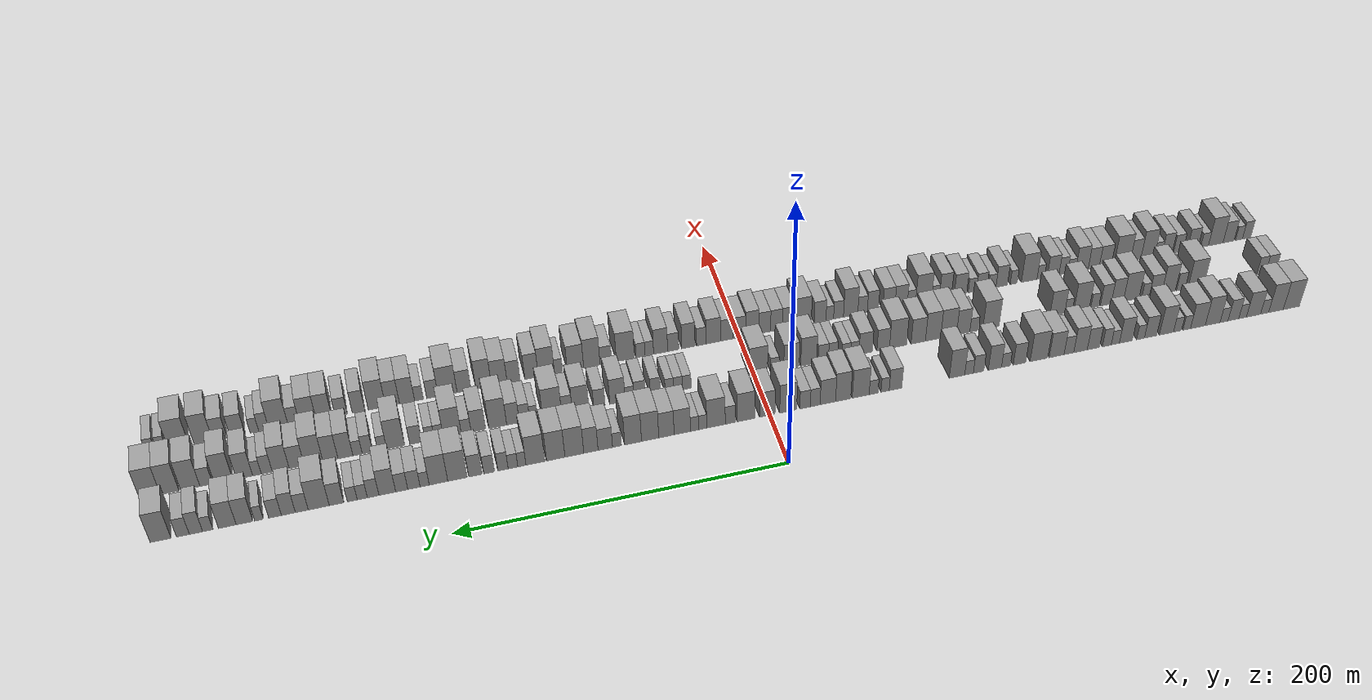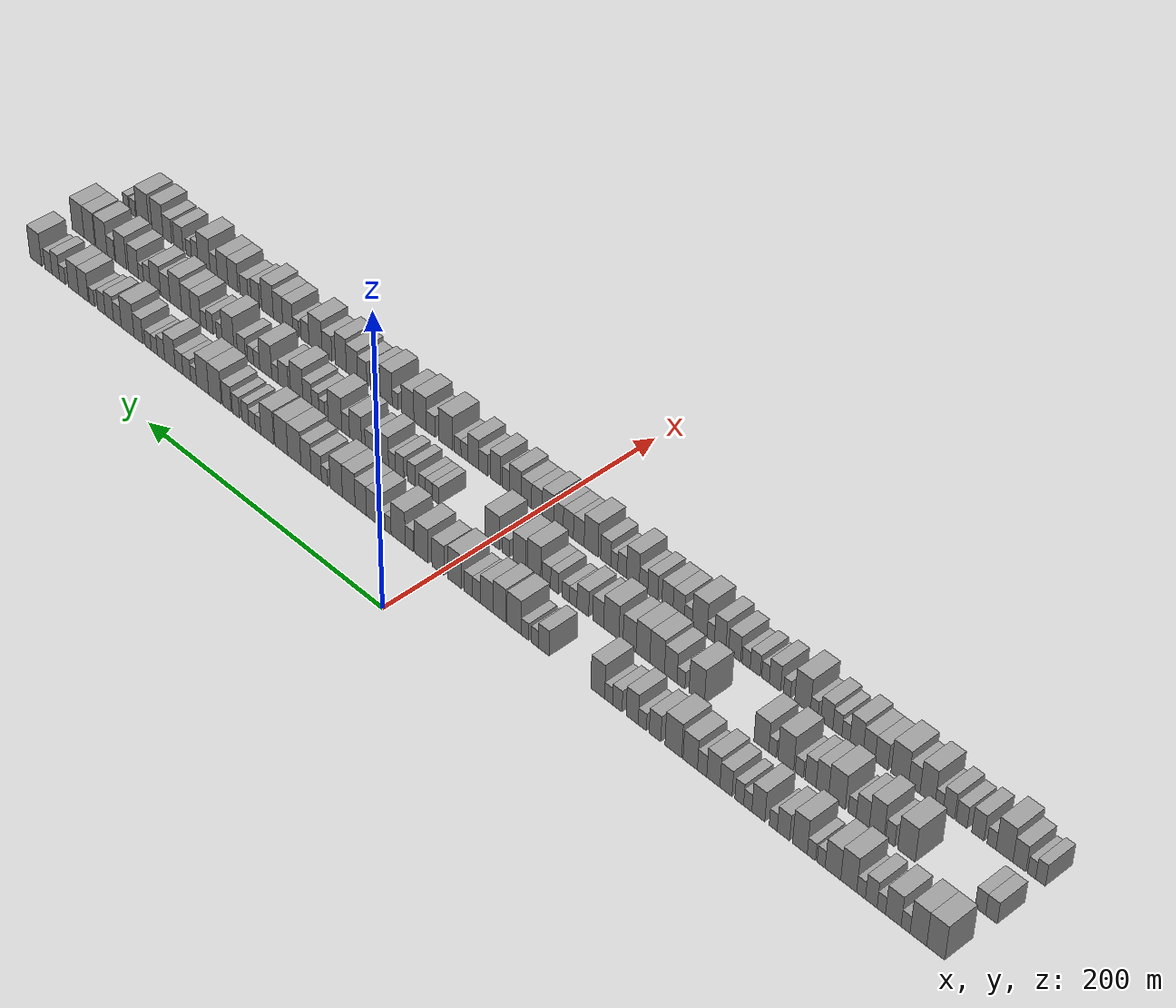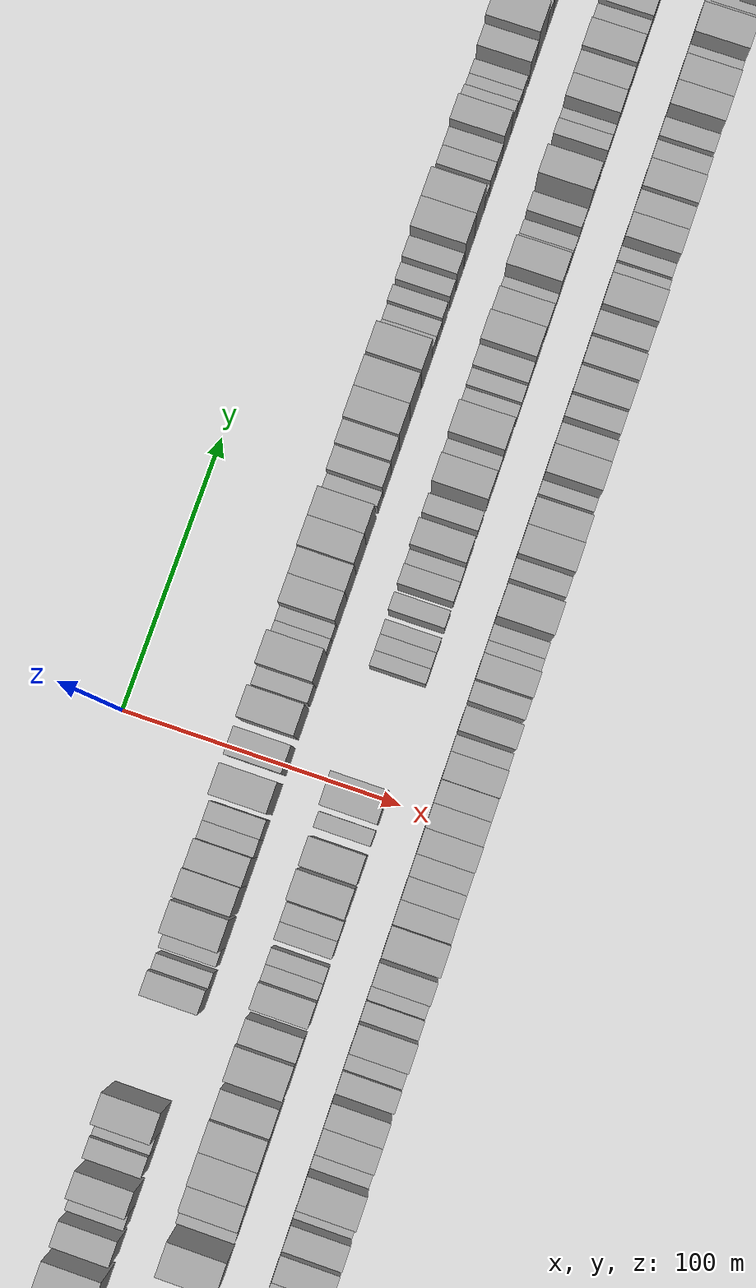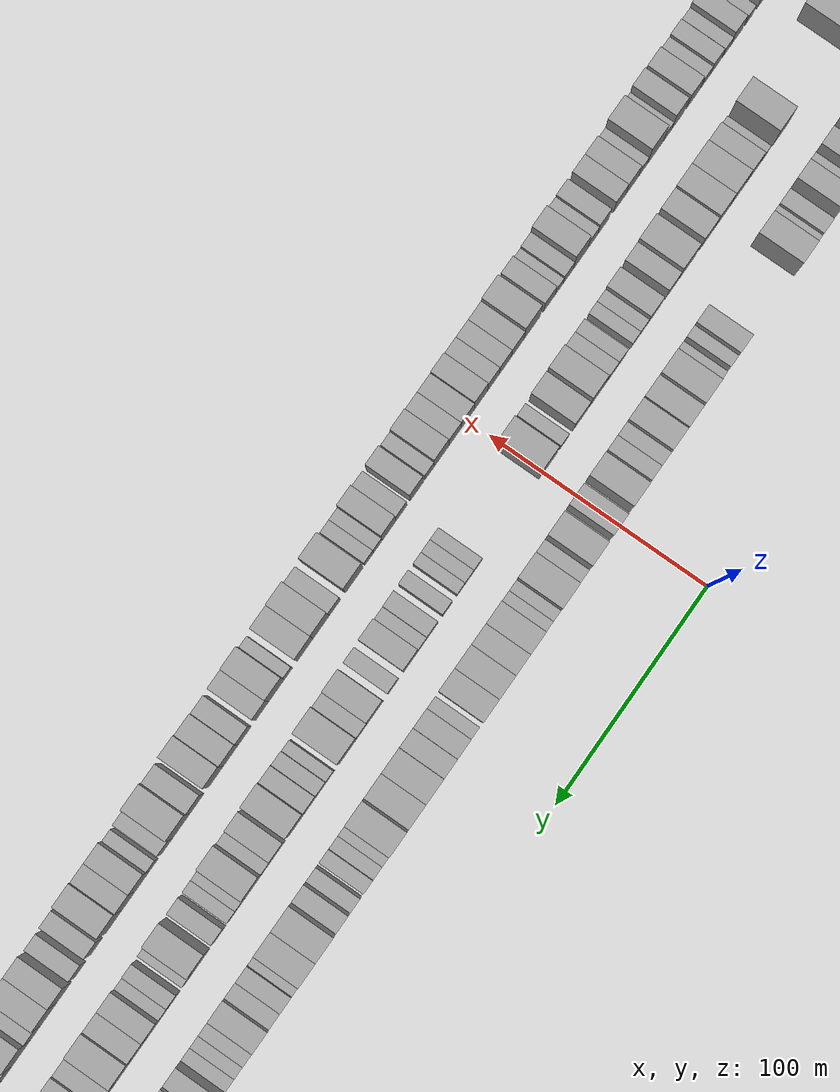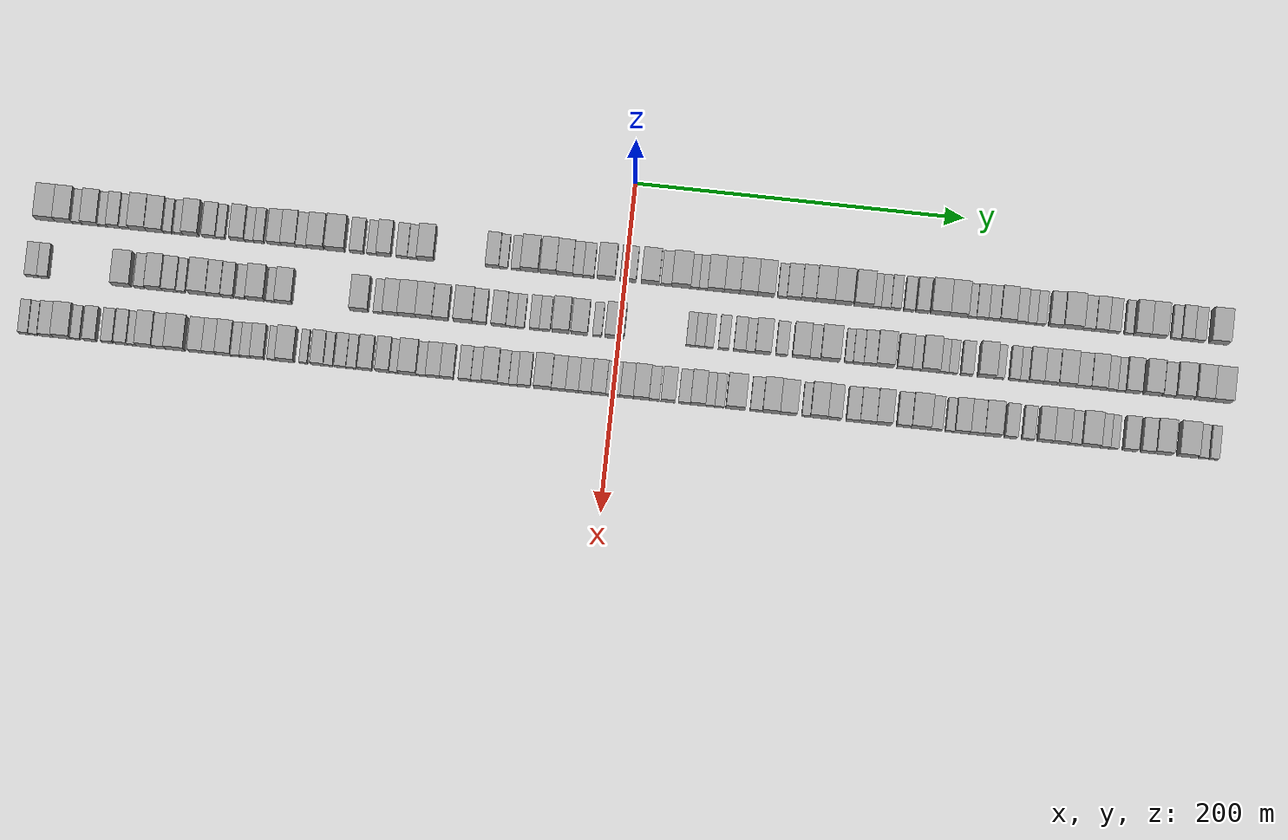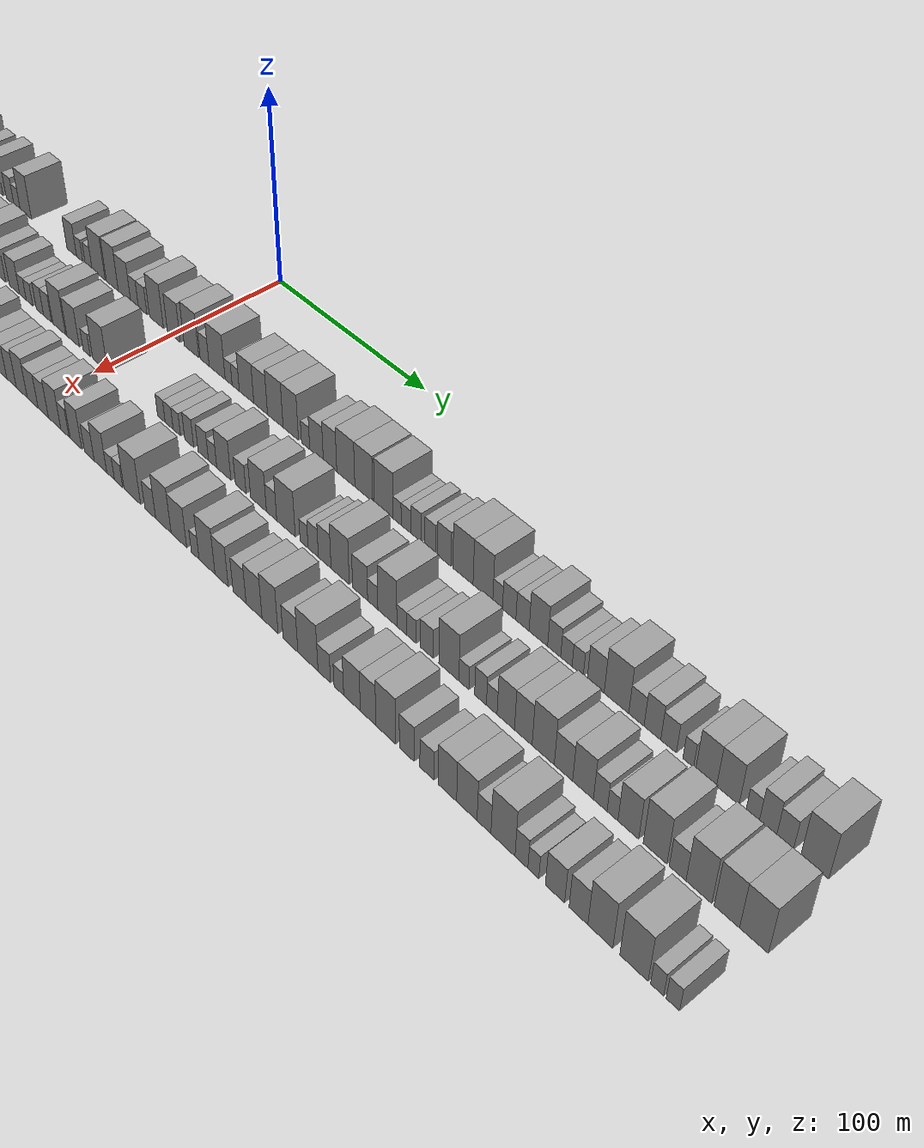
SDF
<sdf version="1.6">
 <world name="default">
  <scene>
   <sky><clouds><speed>12</speed></clouds></sky>
   <ambient>0.4 0.4 0.4 1</ambient>
   <background>0.7 0.7 0.7 1</background>
   <shadows>1</shadows>
  </scene>
  <gravity>0 0 -9.8066</gravity>
  <magnetic_field>6e-06 2.3e-05 -4.2e-05</magnetic_field>
  <physics default="0" name="default_physics" type="ode">
   <ode>
    <solver>
     <type>quick</type>
     <iters>10</iters>
     <sor>1.0</sor>
     <use_dynamic_moi_rescaling>0</use_dynamic_moi_rescaling>
    </solver>
    <constraints>
     <cfm>0</cfm>
     <erp>0.2</erp>
     <contact_max_correcting_vel>100</contact_max_correcting_vel>
     <contact_surface_layer>0.001</contact_surface_layer>
    </constraints>
   </ode>
   <max_step_size>0.004</max_step_size>
   <real_time_factor>1</real_time_factor>
   <real_time_update_rate>250</real_time_update_rate>
  </physics>
  <light name="sun" type="directional">
   <pose>0 0 10 0 0 0</pose>
   <diffuse>0.8 0.8 0.8 1</diffuse>
   <specular>0.2 0.2 0.2 1</specular>
   <attenuation>
    <range>1000</range>
    <constant>0.9</constant>
    <linear>0.01</linear>
    <quadratic>0.001</quadratic>
   </attenuation>
   <direction>-0.5 0.1 -0.9</direction>
  </light>
  <model name="building_1">
   <static>1</static>
   <pose>50.0000 -352.2117 0 0.000000 0.000000 0.000000</pose>
   <link name="link">
    <pose>0 0 12.00 0 0 0</pose>
    <collision name="collision"><geometry><box><size>20.0000 11.5766 24.0000</size></box></geometry></collision>
    <visual name="visual">
     <cast_shadows>0</cast_shadows>
     <geometry><box><size>20.0000 11.5766 24.0000</size></box></geometry>
     <material>
      <script>
       <uri>model://grey_wall/materials/scripts</uri>
       <uri>model://grey_wall/materials/textures</uri>
       <name>vrc/grey_wall</name>
      </script>
     </material>
    </visual>
   </link>
  </model>
  <model name="building_2">
   <static>1</static>
   <pose>50.0000 -341.1481 0 0.000000 0.000000 0.000000</pose>
   <link name="link">
    <pose>0 0 12.00 0 0 0</pose>
    <collision name="collision"><geometry><box><size>20.0000 10.5507 24.0000</size></box></geometry></collision>
    <visual name="visual">
     <cast_shadows>0</cast_shadows>
     <geometry><box><size>20.0000 10.5507 24.0000</size></box></geometry>
     <material>
      <script>
       <uri>model://grey_wall/materials/scripts</uri>
       <uri>model://grey_wall/materials/textures</uri>
       <name>vrc/grey_wall</name>
      </script>
     </material>
    </visual>
   </link>
  </model>
  <model name="building_3">
   <static>1</static>
   <pose>50.0000 -332.9956 0 0.000000 0.000000 0.000000</pose>
   <link name="link">
    <pose>0 0 6.00 0 0 0</pose>
    <collision name="collision"><geometry><box><size>20.0000 5.7543 12.0000</size></box></geometry></collision>
    <visual name="visual">
     <cast_shadows>0</cast_shadows>
     <geometry><box><size>20.0000 5.7543 12.0000</size></box></geometry>
     <material>
      <script>
       <uri>model://grey_wall/materials/scripts</uri>
       <uri>model://grey_wall/materials/textures</uri>
       <name>vrc/grey_wall</name>
      </script>
     </material>
    </visual>
   </link>
  </model>
  <model name="building_4">
   <static>1</static>
   <pose>50.0000 -325.0731 0 0.000000 0.000000 0.000000</pose>
   <link name="link">
    <pose>0 0 10.50 0 0 0</pose>
    <collision name="collision"><geometry><box><size>20.0000 10.0907 21.0000</size></box></geometry></collision>
    <visual name="visual">
     <cast_shadows>0</cast_shadows>
     <geometry><box><size>20.0000 10.0907 21.0000</size></box></geometry>
     <material>
      <script>
       <uri>model://grey_wall/materials/scripts</uri>
       <uri>model://grey_wall/materials/textures</uri>
       <name>vrc/grey_wall</name>
      </script>
     </material>
    </visual>
   </link>
  </model>
  <model name="building_5">
   <static>1</static>
   <pose>50.0000 -317.3118 0 0.000000 0.000000 0.000000</pose>
   <link name="link">
    <pose>0 0 6.00 0 0 0</pose>
    <collision name="collision"><geometry><box><size>20.0000 5.4318 12.0000</size></box></geometry></collision>
    <visual name="visual">
     <cast_shadows>0</cast_shadows>
     <geometry><box><size>20.0000 5.4318 12.0000</size></box></geometry>
     <material>
      <script>
       <uri>model://grey_wall/materials/scripts</uri>
       <uri>model://grey_wall/materials/textures</uri>
       <name>vrc/grey_wall</name>
      </script>
     </material>
    </visual>
   </link>
  </model>
  <model name="building_6">
   <static>1</static>
   <pose>50.0000 -310.7910 0 0.000000 0.000000 0.000000</pose>
   <link name="link">
    <pose>0 0 9.00 0 0 0</pose>
    <collision name="collision"><geometry><box><size>20.0000 7.6099 18.0000</size></box></geometry></collision>
    <visual name="visual">
     <cast_shadows>0</cast_shadows>
     <geometry><box><size>20.0000 7.6099 18.0000</size></box></geometry>
     <material>
      <script>
       <uri>model://grey_wall/materials/scripts</uri>
       <uri>model://grey_wall/materials/textures</uri>
       <name>vrc/grey_wall</name>
      </script>
     </material>
    </visual>
   </link>
  </model>
  <model name="building_7">
   <static>1</static>
   <pose>50.0000 -304.1499 0 0.000000 0.000000 0.000000</pose>
   <link name="link">
    <pose>0 0 6.00 0 0 0</pose>
    <collision name="collision"><geometry><box><size>20.0000 5.6723 12.0000</size></box></geometry></collision>
    <visual name="visual">
     <cast_shadows>0</cast_shadows>
     <geometry><box><size>20.0000 5.6723 12.0000</size></box></geometry>
     <material>
      <script>
       <uri>model://grey_wall/materials/scripts</uri>
       <uri>model://grey_wall/materials/textures</uri>
       <name>vrc/grey_wall</name>
      </script>
     </material>
    </visual>
   </link>
  </model>
  <model name="building_8">
   <static>1</static>
   <pose>50.0000 -296.0833 0 0.000000 0.000000 0.000000</pose>
   <link name="link">
    <pose>0 0 12.00 0 0 0</pose>
    <collision name="collision"><geometry><box><size>20.0000 10.4610 24.0000</size></box></geometry></collision>
    <visual name="visual">
     <cast_shadows>0</cast_shadows>
     <geometry><box><size>20.0000 10.4610 24.0000</size></box></geometry>
     <material>
      <script>
       <uri>model://grey_wall/materials/scripts</uri>
       <uri>model://grey_wall/materials/textures</uri>
       <name>vrc/grey_wall</name>
      </script>
     </material>
    </visual>
   </link>
  </model>
  <model name="building_9">
   <static>1</static>
   <pose>50.0000 -285.6583 0 0.000000 0.000000 0.000000</pose>
   <link name="link">
    <pose>0 0 10.50 0 0 0</pose>
    <collision name="collision"><geometry><box><size>20.0000 10.3890 21.0000</size></box></geometry></collision>
    <visual name="visual">
     <cast_shadows>0</cast_shadows>
     <geometry><box><size>20.0000 10.3890 21.0000</size></box></geometry>
     <material>
      <script>
       <uri>model://grey_wall/materials/scripts</uri>
       <uri>model://grey_wall/materials/textures</uri>
       <name>vrc/grey_wall</name>
      </script>
     </material>
    </visual>
   </link>
  </model>
  <model name="building_10">
   <static>1</static>
   <pose>50.0000 -277.8284 0 0.000000 0.000000 0.000000</pose>
   <link name="link">
    <pose>0 0 6.00 0 0 0</pose>
    <collision name="collision"><geometry><box><size>20.0000 5.2708 12.0000</size></box></geometry></collision>
    <visual name="visual">
     <cast_shadows>0</cast_shadows>
     <geometry><box><size>20.0000 5.2708 12.0000</size></box></geometry>
     <material>
      <script>
       <uri>model://grey_wall/materials/scripts</uri>
       <uri>model://grey_wall/materials/textures</uri>
       <name>vrc/grey_wall</name>
      </script>
     </material>
    </visual>
   </link>
  </model>
  <model name="building_11">
   <static>1</static>
   <pose>50.0000 -271.3896 0 0.000000 0.000000 0.000000</pose>
   <link name="link">
    <pose>0 0 6.00 0 0 0</pose>
    <collision name="collision"><geometry><box><size>20.0000 5.6068 12.0000</size></box></geometry></collision>
    <visual name="visual">
     <cast_shadows>0</cast_shadows>
     <geometry><box><size>20.0000 5.6068 12.0000</size></box></geometry>
     <material>
      <script>
       <uri>model://grey_wall/materials/scripts</uri>
       <uri>model://grey_wall/materials/textures</uri>
       <name>vrc/grey_wall</name>
      </script>
     </material>
    </visual>
   </link>
  </model>
  <model name="building_12">
   <static>1</static>
   <pose>50.0000 -263.6431 0 0.000000 0.000000 0.000000</pose>
   <link name="link">
    <pose>0 0 12.00 0 0 0</pose>
    <collision name="collision"><geometry><box><size>20.0000 9.8863 24.0000</size></box></geometry></collision>
    <visual name="visual">
     <cast_shadows>0</cast_shadows>
     <geometry><box><size>20.0000 9.8863 24.0000</size></box></geometry>
     <material>
      <script>
       <uri>model://grey_wall/materials/scripts</uri>
       <uri>model://grey_wall/materials/textures</uri>
       <name>vrc/grey_wall</name>
      </script>
     </material>
    </visual>
   </link>
  </model>
  <model name="building_13">
   <static>1</static>
   <pose>50.0000 -252.4964 0 0.000000 0.000000 0.000000</pose>
   <link name="link">
    <pose>0 0 9.00 0 0 0</pose>
    <collision name="collision"><geometry><box><size>20.0000 8.4071 18.0000</size></box></geometry></collision>
    <visual name="visual">
     <cast_shadows>0</cast_shadows>
     <geometry><box><size>20.0000 8.4071 18.0000</size></box></geometry>
     <material>
      <script>
       <uri>model://grey_wall/materials/scripts</uri>
       <uri>model://grey_wall/materials/textures</uri>
       <name>vrc/grey_wall</name>
      </script>
     </material>
    </visual>
   </link>
  </model>
  <model name="building_14">
   <static>1</static>
   <pose>50.0000 -245.5898 0 0.000000 0.000000 0.000000</pose>
   <link name="link">
    <pose>0 0 6.00 0 0 0</pose>
    <collision name="collision"><geometry><box><size>20.0000 5.4060 12.0000</size></box></geometry></collision>
    <visual name="visual">
     <cast_shadows>0</cast_shadows>
     <geometry><box><size>20.0000 5.4060 12.0000</size></box></geometry>
     <material>
      <script>
       <uri>model://grey_wall/materials/scripts</uri>
       <uri>model://grey_wall/materials/textures</uri>
       <name>vrc/grey_wall</name>
      </script>
     </material>
    </visual>
   </link>
  </model>
  <model name="building_15">
   <static>1</static>
   <pose>50.0000 -235.4230 0 0.000000 0.000000 0.000000</pose>
   <link name="link">
    <pose>0 0 10.50 0 0 0</pose>
    <collision name="collision"><geometry><box><size>20.0000 8.9276 21.0000</size></box></geometry></collision>
    <visual name="visual">
     <cast_shadows>0</cast_shadows>
     <geometry><box><size>20.0000 8.9276 21.0000</size></box></geometry>
     <material>
      <script>
       <uri>model://grey_wall/materials/scripts</uri>
       <uri>model://grey_wall/materials/textures</uri>
       <name>vrc/grey_wall</name>
      </script>
     </material>
    </visual>
   </link>
  </model>
  <model name="building_16">
   <static>1</static>
   <pose>50.0000 -228.1357 0 0.000000 0.000000 0.000000</pose>
   <link name="link">
    <pose>0 0 6.00 0 0 0</pose>
    <collision name="collision"><geometry><box><size>20.0000 5.6471 12.0000</size></box></geometry></collision>
    <visual name="visual">
     <cast_shadows>0</cast_shadows>
     <geometry><box><size>20.0000 5.6471 12.0000</size></box></geometry>
     <material>
      <script>
       <uri>model://grey_wall/materials/scripts</uri>
       <uri>model://grey_wall/materials/textures</uri>
       <name>vrc/grey_wall</name>
      </script>
     </material>
    </visual>
   </link>
  </model>
  <model name="building_17">
   <static>1</static>
   <pose>50.0000 -222.2923 0 0.000000 0.000000 0.000000</pose>
   <link name="link">
    <pose>0 0 7.50 0 0 0</pose>
    <collision name="collision"><geometry><box><size>20.0000 6.0396 15.0000</size></box></geometry></collision>
    <visual name="visual">
     <cast_shadows>0</cast_shadows>
     <geometry><box><size>20.0000 6.0396 15.0000</size></box></geometry>
     <material>
      <script>
       <uri>model://grey_wall/materials/scripts</uri>
       <uri>model://grey_wall/materials/textures</uri>
       <name>vrc/grey_wall</name>
      </script>
     </material>
    </visual>
   </link>
  </model>
  <model name="building_18">
   <static>1</static>
   <pose>50.0000 -213.0704 0 0.000000 0.000000 0.000000</pose>
   <link name="link">
    <pose>0 0 9.00 0 0 0</pose>
    <collision name="collision"><geometry><box><size>20.0000 8.4042 18.0000</size></box></geometry></collision>
    <visual name="visual">
     <cast_shadows>0</cast_shadows>
     <geometry><box><size>20.0000 8.4042 18.0000</size></box></geometry>
     <material>
      <script>
       <uri>model://grey_wall/materials/scripts</uri>
       <uri>model://grey_wall/materials/textures</uri>
       <name>vrc/grey_wall</name>
      </script>
     </material>
    </visual>
   </link>
  </model>
  <model name="building_19">
   <static>1</static>
   <pose>50.0000 -204.2598 0 0.000000 0.000000 0.000000</pose>
   <link name="link">
    <pose>0 0 10.50 0 0 0</pose>
    <collision name="collision"><geometry><box><size>20.0000 9.2172 21.0000</size></box></geometry></collision>
    <visual name="visual">
     <cast_shadows>0</cast_shadows>
     <geometry><box><size>20.0000 9.2172 21.0000</size></box></geometry>
     <material>
      <script>
       <uri>model://grey_wall/materials/scripts</uri>
       <uri>model://grey_wall/materials/textures</uri>
       <name>vrc/grey_wall</name>
      </script>
     </material>
    </visual>
   </link>
  </model>
  <model name="building_20">
   <static>1</static>
   <pose>50.0000 -196.3667 0 0.000000 0.000000 0.000000</pose>
   <link name="link">
    <pose>0 0 7.50 0 0 0</pose>
    <collision name="collision"><geometry><box><size>20.0000 6.5690 15.0000</size></box></geometry></collision>
    <visual name="visual">
     <cast_shadows>0</cast_shadows>
     <geometry><box><size>20.0000 6.5690 15.0000</size></box></geometry>
     <material>
      <script>
       <uri>model://grey_wall/materials/scripts</uri>
       <uri>model://grey_wall/materials/textures</uri>
       <name>vrc/grey_wall</name>
      </script>
     </material>
    </visual>
   </link>
  </model>
  <model name="building_21">
   <static>1</static>
   <pose>50.0000 -188.0146 0 0.000000 0.000000 0.000000</pose>
   <link name="link">
    <pose>0 0 10.50 0 0 0</pose>
    <collision name="collision"><geometry><box><size>20.0000 10.1351 21.0000</size></box></geometry></collision>
    <visual name="visual">
     <cast_shadows>0</cast_shadows>
     <geometry><box><size>20.0000 10.1351 21.0000</size></box></geometry>
     <material>
      <script>
       <uri>model://grey_wall/materials/scripts</uri>
       <uri>model://grey_wall/materials/textures</uri>
       <name>vrc/grey_wall</name>
      </script>
     </material>
    </visual>
   </link>
  </model>
  <model name="building_22">
   <static>1</static>
   <pose>50.0000 -175.9941 0 0.000000 0.000000 0.000000</pose>
   <link name="link">
    <pose>0 0 12.00 0 0 0</pose>
    <collision name="collision"><geometry><box><size>20.0000 11.9061 24.0000</size></box></geometry></collision>
    <visual name="visual">
     <cast_shadows>0</cast_shadows>
     <geometry><box><size>20.0000 11.9061 24.0000</size></box></geometry>
     <material>
      <script>
       <uri>model://grey_wall/materials/scripts</uri>
       <uri>model://grey_wall/materials/textures</uri>
       <name>vrc/grey_wall</name>
      </script>
     </material>
    </visual>
   </link>
  </model>
  <model name="building_23">
   <static>1</static>
   <pose>50.0000 -162.8653 0 0.000000 0.000000 0.000000</pose>
   <link name="link">
    <pose>0 0 9.00 0 0 0</pose>
    <collision name="collision"><geometry><box><size>20.0000 8.3515 18.0000</size></box></geometry></collision>
    <visual name="visual">
     <cast_shadows>0</cast_shadows>
     <geometry><box><size>20.0000 8.3515 18.0000</size></box></geometry>
     <material>
      <script>
       <uri>model://grey_wall/materials/scripts</uri>
       <uri>model://grey_wall/materials/textures</uri>
       <name>vrc/grey_wall</name>
      </script>
     </material>
    </visual>
   </link>
  </model>
  <model name="building_24">
   <static>1</static>
   <pose>50.0000 -153.7369 0 0.000000 0.000000 0.000000</pose>
   <link name="link">
    <pose>0 0 6.00 0 0 0</pose>
    <collision name="collision"><geometry><box><size>20.0000 5.9052 12.0000</size></box></geometry></collision>
    <visual name="visual">
     <cast_shadows>0</cast_shadows>
     <geometry><box><size>20.0000 5.9052 12.0000</size></box></geometry>
     <material>
      <script>
       <uri>model://grey_wall/materials/scripts</uri>
       <uri>model://grey_wall/materials/textures</uri>
       <name>vrc/grey_wall</name>
      </script>
     </material>
    </visual>
   </link>
  </model>
  <model name="building_25">
   <static>1</static>
   <pose>50.0000 -146.3802 0 0.000000 0.000000 0.000000</pose>
   <link name="link">
    <pose>0 0 10.50 0 0 0</pose>
    <collision name="collision"><geometry><box><size>20.0000 8.8084 21.0000</size></box></geometry></collision>
    <visual name="visual">
     <cast_shadows>0</cast_shadows>
     <geometry><box><size>20.0000 8.8084 21.0000</size></box></geometry>
     <material>
      <script>
       <uri>model://grey_wall/materials/scripts</uri>
       <uri>model://grey_wall/materials/textures</uri>
       <name>vrc/grey_wall</name>
      </script>
     </material>
    </visual>
   </link>
  </model>
  <model name="building_26">
   <static>1</static>
   <pose>50.0000 -135.5037 0 0.000000 0.000000 0.000000</pose>
   <link name="link">
    <pose>0 0 7.50 0 0 0</pose>
    <collision name="collision"><geometry><box><size>20.0000 6.9447 15.0000</size></box></geometry></collision>
    <visual name="visual">
     <cast_shadows>0</cast_shadows>
     <geometry><box><size>20.0000 6.9447 15.0000</size></box></geometry>
     <material>
      <script>
       <uri>model://grey_wall/materials/scripts</uri>
       <uri>model://grey_wall/materials/textures</uri>
       <name>vrc/grey_wall</name>
      </script>
     </material>
    </visual>
   </link>
  </model>
  <model name="building_27">
   <static>1</static>
   <pose>50.0000 -129.1409 0 0.000000 0.000000 0.000000</pose>
   <link name="link">
    <pose>0 0 6.00 0 0 0</pose>
    <collision name="collision"><geometry><box><size>20.0000 5.7808 12.0000</size></box></geometry></collision>
    <visual name="visual">
     <cast_shadows>0</cast_shadows>
     <geometry><box><size>20.0000 5.7808 12.0000</size></box></geometry>
     <material>
      <script>
       <uri>model://grey_wall/materials/scripts</uri>
       <uri>model://grey_wall/materials/textures</uri>
       <name>vrc/grey_wall</name>
      </script>
     </material>
    </visual>
   </link>
  </model>
  <model name="building_28">
   <static>1</static>
   <pose>50.0000 -121.1450 0 0.000000 0.000000 0.000000</pose>
   <link name="link">
    <pose>0 0 12.00 0 0 0</pose>
    <collision name="collision"><geometry><box><size>20.0000 10.2110 24.0000</size></box></geometry></collision>
    <visual name="visual">
     <cast_shadows>0</cast_shadows>
     <geometry><box><size>20.0000 10.2110 24.0000</size></box></geometry>
     <material>
      <script>
       <uri>model://grey_wall/materials/scripts</uri>
       <uri>model://grey_wall/materials/textures</uri>
       <name>vrc/grey_wall</name>
      </script>
     </material>
    </visual>
   </link>
  </model>
  <model name="building_29">
   <static>1</static>
   <pose>50.0000 -80.6771 0 0.000000 0.000000 0.000000</pose>
   <link name="link">
    <pose>0 0 9.00 0 0 0</pose>
    <collision name="collision"><geometry><box><size>20.0000 8.2416 18.0000</size></box></geometry></collision>
    <visual name="visual">
     <cast_shadows>0</cast_shadows>
     <geometry><box><size>20.0000 8.2416 18.0000</size></box></geometry>
     <material>
      <script>
       <uri>model://grey_wall/materials/scripts</uri>
       <uri>model://grey_wall/materials/textures</uri>
       <name>vrc/grey_wall</name>
      </script>
     </material>
    </visual>
   </link>
  </model>
  <model name="building_30">
   <static>1</static>
   <pose>50.0000 -73.9138 0 0.000000 0.000000 0.000000</pose>
   <link name="link">
    <pose>0 0 6.00 0 0 0</pose>
    <collision name="collision"><geometry><box><size>20.0000 5.2849 12.0000</size></box></geometry></collision>
    <visual name="visual">
     <cast_shadows>0</cast_shadows>
     <geometry><box><size>20.0000 5.2849 12.0000</size></box></geometry>
     <material>
      <script>
       <uri>model://grey_wall/materials/scripts</uri>
       <uri>model://grey_wall/materials/textures</uri>
       <name>vrc/grey_wall</name>
      </script>
     </material>
    </visual>
   </link>
  </model>
  <model name="building_31">
   <static>1</static>
   <pose>50.0000 -66.4016 0 0.000000 0.000000 0.000000</pose>
   <link name="link">
    <pose>0 0 6.00 0 0 0</pose>
    <collision name="collision"><geometry><box><size>20.0000 5.7396 12.0000</size></box></geometry></collision>
    <visual name="visual">
     <cast_shadows>0</cast_shadows>
     <geometry><box><size>20.0000 5.7396 12.0000</size></box></geometry>
     <material>
      <script>
       <uri>model://grey_wall/materials/scripts</uri>
       <uri>model://grey_wall/materials/textures</uri>
       <name>vrc/grey_wall</name>
      </script>
     </material>
    </visual>
   </link>
  </model>
  <model name="building_32">
   <static>1</static>
   <pose>50.0000 -58.0691 0 0.000000 0.000000 0.000000</pose>
   <link name="link">
    <pose>0 0 12.00 0 0 0</pose>
    <collision name="collision"><geometry><box><size>20.0000 10.9255 24.0000</size></box></geometry></collision>
    <visual name="visual">
     <cast_shadows>0</cast_shadows>
     <geometry><box><size>20.0000 10.9255 24.0000</size></box></geometry>
     <material>
      <script>
       <uri>model://grey_wall/materials/scripts</uri>
       <uri>model://grey_wall/materials/textures</uri>
       <name>vrc/grey_wall</name>
      </script>
     </material>
    </visual>
   </link>
  </model>
  <model name="building_33">
   <static>1</static>
   <pose>50.0000 -46.7354 0 0.000000 0.000000 0.000000</pose>
   <link name="link">
    <pose>0 0 12.00 0 0 0</pose>
    <collision name="collision"><geometry><box><size>20.0000 9.7419 24.0000</size></box></geometry></collision>
    <visual name="visual">
     <cast_shadows>0</cast_shadows>
     <geometry><box><size>20.0000 9.7419 24.0000</size></box></geometry>
     <material>
      <script>
       <uri>model://grey_wall/materials/scripts</uri>
       <uri>model://grey_wall/materials/textures</uri>
       <name>vrc/grey_wall</name>
      </script>
     </material>
    </visual>
   </link>
  </model>
  <model name="building_34">
   <static>1</static>
   <pose>50.0000 -36.8863 0 0.000000 0.000000 0.000000</pose>
   <link name="link">
    <pose>0 0 10.50 0 0 0</pose>
    <collision name="collision"><geometry><box><size>20.0000 9.9563 21.0000</size></box></geometry></collision>
    <visual name="visual">
     <cast_shadows>0</cast_shadows>
     <geometry><box><size>20.0000 9.9563 21.0000</size></box></geometry>
     <material>
      <script>
       <uri>model://grey_wall/materials/scripts</uri>
       <uri>model://grey_wall/materials/textures</uri>
       <name>vrc/grey_wall</name>
      </script>
     </material>
    </visual>
   </link>
  </model>
  <model name="building_35">
   <static>1</static>
   <pose>50.0000 -28.7906 0 0.000000 0.000000 0.000000</pose>
   <link name="link">
    <pose>0 0 7.50 0 0 0</pose>
    <collision name="collision"><geometry><box><size>20.0000 6.2351 15.0000</size></box></geometry></collision>
    <visual name="visual">
     <cast_shadows>0</cast_shadows>
     <geometry><box><size>20.0000 6.2351 15.0000</size></box></geometry>
     <material>
      <script>
       <uri>model://grey_wall/materials/scripts</uri>
       <uri>model://grey_wall/materials/textures</uri>
       <name>vrc/grey_wall</name>
      </script>
     </material>
    </visual>
   </link>
  </model>
  <model name="building_36">
   <static>1</static>
   <pose>50.0000 -22.3189 0 0.000000 0.000000 0.000000</pose>
   <link name="link">
    <pose>0 0 7.50 0 0 0</pose>
    <collision name="collision"><geometry><box><size>20.0000 6.7085 15.0000</size></box></geometry></collision>
    <visual name="visual">
     <cast_shadows>0</cast_shadows>
     <geometry><box><size>20.0000 6.7085 15.0000</size></box></geometry>
     <material>
      <script>
       <uri>model://grey_wall/materials/scripts</uri>
       <uri>model://grey_wall/materials/textures</uri>
       <name>vrc/grey_wall</name>
      </script>
     </material>
    </visual>
   </link>
  </model>
  <model name="building_37">
   <static>1</static>
   <pose>50.0000 -11.5609 0 0.000000 0.000000 0.000000</pose>
   <link name="link">
    <pose>0 0 12.00 0 0 0</pose>
    <collision name="collision"><geometry><box><size>20.0000 10.8074 24.0000</size></box></geometry></collision>
    <visual name="visual">
     <cast_shadows>0</cast_shadows>
     <geometry><box><size>20.0000 10.8074 24.0000</size></box></geometry>
     <material>
      <script>
       <uri>model://grey_wall/materials/scripts</uri>
       <uri>model://grey_wall/materials/textures</uri>
       <name>vrc/grey_wall</name>
      </script>
     </material>
    </visual>
   </link>
  </model>
  <model name="building_38">
   <static>1</static>
   <pose>50.0000 1.7379 0 0.000000 0.000000 0.000000</pose>
   <link name="link">
    <pose>0 0 10.50 0 0 0</pose>
    <collision name="collision"><geometry><box><size>20.0000 9.7903 21.0000</size></box></geometry></collision>
    <visual name="visual">
     <cast_shadows>0</cast_shadows>
     <geometry><box><size>20.0000 9.7903 21.0000</size></box></geometry>
     <material>
      <script>
       <uri>model://grey_wall/materials/scripts</uri>
       <uri>model://grey_wall/materials/textures</uri>
       <name>vrc/grey_wall</name>
      </script>
     </material>
    </visual>
   </link>
  </model>
  <model name="building_39">
   <static>1</static>
   <pose>50.0000 15.1060 0 0.000000 0.000000 0.000000</pose>
   <link name="link">
    <pose>0 0 12.00 0 0 0</pose>
    <collision name="collision"><geometry><box><size>20.0000 10.9457 24.0000</size></box></geometry></collision>
    <visual name="visual">
     <cast_shadows>0</cast_shadows>
     <geometry><box><size>20.0000 10.9457 24.0000</size></box></geometry>
     <material>
      <script>
       <uri>model://grey_wall/materials/scripts</uri>
       <uri>model://grey_wall/materials/textures</uri>
       <name>vrc/grey_wall</name>
      </script>
     </material>
    </visual>
   </link>
  </model>
  <model name="building_40">
   <static>1</static>
   <pose>50.0000 24.8691 0 0.000000 0.000000 0.000000</pose>
   <link name="link">
    <pose>0 0 7.50 0 0 0</pose>
    <collision name="collision"><geometry><box><size>20.0000 6.5806 15.0000</size></box></geometry></collision>
    <visual name="visual">
     <cast_shadows>0</cast_shadows>
     <geometry><box><size>20.0000 6.5806 15.0000</size></box></geometry>
     <material>
      <script>
       <uri>model://grey_wall/materials/scripts</uri>
       <uri>model://grey_wall/materials/textures</uri>
       <name>vrc/grey_wall</name>
      </script>
     </material>
    </visual>
   </link>
  </model>
  <model name="building_41">
   <static>1</static>
   <pose>50.0000 33.9484 0 0.000000 0.000000 0.000000</pose>
   <link name="link">
    <pose>0 0 12.00 0 0 0</pose>
    <collision name="collision"><geometry><box><size>20.0000 11.5780 24.0000</size></box></geometry></collision>
    <visual name="visual">
     <cast_shadows>0</cast_shadows>
     <geometry><box><size>20.0000 11.5780 24.0000</size></box></geometry>
     <material>
      <script>
       <uri>model://grey_wall/materials/scripts</uri>
       <uri>model://grey_wall/materials/textures</uri>
       <name>vrc/grey_wall</name>
      </script>
     </material>
    </visual>
   </link>
  </model>
  <model name="building_42">
   <static>1</static>
   <pose>50.0000 42.2119 0 0.000000 0.000000 0.000000</pose>
   <link name="link">
    <pose>0 0 6.00 0 0 0</pose>
    <collision name="collision"><geometry><box><size>20.0000 4.9488 12.0000</size></box></geometry></collision>
    <visual name="visual">
     <cast_shadows>0</cast_shadows>
     <geometry><box><size>20.0000 4.9488 12.0000</size></box></geometry>
     <material>
      <script>
       <uri>model://grey_wall/materials/scripts</uri>
       <uri>model://grey_wall/materials/textures</uri>
       <name>vrc/grey_wall</name>
      </script>
     </material>
    </visual>
   </link>
  </model>
  <model name="building_43">
   <static>1</static>
   <pose>50.0000 47.2695 0 0.000000 0.000000 0.000000</pose>
   <link name="link">
    <pose>0 0 6.00 0 0 0</pose>
    <collision name="collision"><geometry><box><size>20.0000 5.1664 12.0000</size></box></geometry></collision>
    <visual name="visual">
     <cast_shadows>0</cast_shadows>
     <geometry><box><size>20.0000 5.1664 12.0000</size></box></geometry>
     <material>
      <script>
       <uri>model://grey_wall/materials/scripts</uri>
       <uri>model://grey_wall/materials/textures</uri>
       <name>vrc/grey_wall</name>
      </script>
     </material>
    </visual>
   </link>
  </model>
  <model name="building_44">
   <static>1</static>
   <pose>50.0000 54.9293 0 0.000000 0.000000 0.000000</pose>
   <link name="link">
    <pose>0 0 10.50 0 0 0</pose>
    <collision name="collision"><geometry><box><size>20.0000 10.1532 21.0000</size></box></geometry></collision>
    <visual name="visual">
     <cast_shadows>0</cast_shadows>
     <geometry><box><size>20.0000 10.1532 21.0000</size></box></geometry>
     <material>
      <script>
       <uri>model://grey_wall/materials/scripts</uri>
       <uri>model://grey_wall/materials/textures</uri>
       <name>vrc/grey_wall</name>
      </script>
     </material>
    </visual>
   </link>
  </model>
  <model name="building_45">
   <static>1</static>
   <pose>50.0000 64.7519 0 0.000000 0.000000 0.000000</pose>
   <link name="link">
    <pose>0 0 10.50 0 0 0</pose>
    <collision name="collision"><geometry><box><size>20.0000 9.4919 21.0000</size></box></geometry></collision>
    <visual name="visual">
     <cast_shadows>0</cast_shadows>
     <geometry><box><size>20.0000 9.4919 21.0000</size></box></geometry>
     <material>
      <script>
       <uri>model://grey_wall/materials/scripts</uri>
       <uri>model://grey_wall/materials/textures</uri>
       <name>vrc/grey_wall</name>
      </script>
     </material>
    </visual>
   </link>
  </model>
  <model name="building_46">
   <static>1</static>
   <pose>50.0000 74.7972 0 0.000000 0.000000 0.000000</pose>
   <link name="link">
    <pose>0 0 12.00 0 0 0</pose>
    <collision name="collision"><geometry><box><size>20.0000 10.5988 24.0000</size></box></geometry></collision>
    <visual name="visual">
     <cast_shadows>0</cast_shadows>
     <geometry><box><size>20.0000 10.5988 24.0000</size></box></geometry>
     <material>
      <script>
       <uri>model://grey_wall/materials/scripts</uri>
       <uri>model://grey_wall/materials/textures</uri>
       <name>vrc/grey_wall</name>
      </script>
     </material>
    </visual>
   </link>
  </model>
  <model name="building_47">
   <static>1</static>
   <pose>50.0000 85.2420 0 0.000000 0.000000 0.000000</pose>
   <link name="link">
    <pose>0 0 12.00 0 0 0</pose>
    <collision name="collision"><geometry><box><size>20.0000 10.2908 24.0000</size></box></geometry></collision>
    <visual name="visual">
     <cast_shadows>0</cast_shadows>
     <geometry><box><size>20.0000 10.2908 24.0000</size></box></geometry>
     <material>
      <script>
       <uri>model://grey_wall/materials/scripts</uri>
       <uri>model://grey_wall/materials/textures</uri>
       <name>vrc/grey_wall</name>
      </script>
     </material>
    </visual>
   </link>
  </model>
  <model name="building_48">
   <static>1</static>
   <pose>50.0000 95.1139 0 0.000000 0.000000 0.000000</pose>
   <link name="link">
    <pose>0 0 6.00 0 0 0</pose>
    <collision name="collision"><geometry><box><size>20.0000 5.4530 12.0000</size></box></geometry></collision>
    <visual name="visual">
     <cast_shadows>0</cast_shadows>
     <geometry><box><size>20.0000 5.4530 12.0000</size></box></geometry>
     <material>
      <script>
       <uri>model://grey_wall/materials/scripts</uri>
       <uri>model://grey_wall/materials/textures</uri>
       <name>vrc/grey_wall</name>
      </script>
     </material>
    </visual>
   </link>
  </model>
  <model name="building_49">
   <static>1</static>
   <pose>50.0000 102.2486 0 0.000000 0.000000 0.000000</pose>
   <link name="link">
    <pose>0 0 9.00 0 0 0</pose>
    <collision name="collision"><geometry><box><size>20.0000 8.8165 18.0000</size></box></geometry></collision>
    <visual name="visual">
     <cast_shadows>0</cast_shadows>
     <geometry><box><size>20.0000 8.8165 18.0000</size></box></geometry>
     <material>
      <script>
       <uri>model://grey_wall/materials/scripts</uri>
       <uri>model://grey_wall/materials/textures</uri>
       <name>vrc/grey_wall</name>
      </script>
     </material>
    </visual>
   </link>
  </model>
  <model name="building_50">
   <static>1</static>
   <pose>50.0000 110.9926 0 0.000000 0.000000 0.000000</pose>
   <link name="link">
    <pose>0 0 10.50 0 0 0</pose>
    <collision name="collision"><geometry><box><size>20.0000 8.6714 21.0000</size></box></geometry></collision>
    <visual name="visual">
     <cast_shadows>0</cast_shadows>
     <geometry><box><size>20.0000 8.6714 21.0000</size></box></geometry>
     <material>
      <script>
       <uri>model://grey_wall/materials/scripts</uri>
       <uri>model://grey_wall/materials/textures</uri>
       <name>vrc/grey_wall</name>
      </script>
     </material>
    </visual>
   </link>
  </model>
  <model name="building_51">
   <static>1</static>
   <pose>50.0000 121.0256 0 0.000000 0.000000 0.000000</pose>
   <link name="link">
    <pose>0 0 12.00 0 0 0</pose>
    <collision name="collision"><geometry><box><size>20.0000 11.3945 24.0000</size></box></geometry></collision>
    <visual name="visual">
     <cast_shadows>0</cast_shadows>
     <geometry><box><size>20.0000 11.3945 24.0000</size></box></geometry>
     <material>
      <script>
       <uri>model://grey_wall/materials/scripts</uri>
       <uri>model://grey_wall/materials/textures</uri>
       <name>vrc/grey_wall</name>
      </script>
     </material>
    </visual>
   </link>
  </model>
  <model name="building_52">
   <static>1</static>
   <pose>50.0000 132.2660 0 0.000000 0.000000 0.000000</pose>
   <link name="link">
    <pose>0 0 12.00 0 0 0</pose>
    <collision name="collision"><geometry><box><size>20.0000 11.0864 24.0000</size></box></geometry></collision>
    <visual name="visual">
     <cast_shadows>0</cast_shadows>
     <geometry><box><size>20.0000 11.0864 24.0000</size></box></geometry>
     <material>
      <script>
       <uri>model://grey_wall/materials/scripts</uri>
       <uri>model://grey_wall/materials/textures</uri>
       <name>vrc/grey_wall</name>
      </script>
     </material>
    </visual>
   </link>
  </model>
  <model name="building_53">
   <static>1</static>
   <pose>50.0000 144.4724 0 0.000000 0.000000 0.000000</pose>
   <link name="link">
    <pose>0 0 12.00 0 0 0</pose>
    <collision name="collision"><geometry><box><size>20.0000 11.3264 24.0000</size></box></geometry></collision>
    <visual name="visual">
     <cast_shadows>0</cast_shadows>
     <geometry><box><size>20.0000 11.3264 24.0000</size></box></geometry>
     <material>
      <script>
       <uri>model://grey_wall/materials/scripts</uri>
       <uri>model://grey_wall/materials/textures</uri>
       <name>vrc/grey_wall</name>
      </script>
     </material>
    </visual>
   </link>
  </model>
  <model name="building_54">
   <static>1</static>
   <pose>50.0000 152.5741 0 0.000000 0.000000 0.000000</pose>
   <link name="link">
    <pose>0 0 6.00 0 0 0</pose>
    <collision name="collision"><geometry><box><size>20.0000 4.8770 12.0000</size></box></geometry></collision>
    <visual name="visual">
     <cast_shadows>0</cast_shadows>
     <geometry><box><size>20.0000 4.8770 12.0000</size></box></geometry>
     <material>
      <script>
       <uri>model://grey_wall/materials/scripts</uri>
       <uri>model://grey_wall/materials/textures</uri>
       <name>vrc/grey_wall</name>
      </script>
     </material>
    </visual>
   </link>
  </model>
  <model name="building_55">
   <static>1</static>
   <pose>50.0000 157.9040 0 0.000000 0.000000 0.000000</pose>
   <link name="link">
    <pose>0 0 6.00 0 0 0</pose>
    <collision name="collision"><geometry><box><size>20.0000 5.7828 12.0000</size></box></geometry></collision>
    <visual name="visual">
     <cast_shadows>0</cast_shadows>
     <geometry><box><size>20.0000 5.7828 12.0000</size></box></geometry>
     <material>
      <script>
       <uri>model://grey_wall/materials/scripts</uri>
       <uri>model://grey_wall/materials/textures</uri>
       <name>vrc/grey_wall</name>
      </script>
     </material>
    </visual>
   </link>
  </model>
  <model name="building_56">
   <static>1</static>
   <pose>50.0000 163.8397 0 0.000000 0.000000 0.000000</pose>
   <link name="link">
    <pose>0 0 7.50 0 0 0</pose>
    <collision name="collision"><geometry><box><size>20.0000 6.0886 15.0000</size></box></geometry></collision>
    <visual name="visual">
     <cast_shadows>0</cast_shadows>
     <geometry><box><size>20.0000 6.0886 15.0000</size></box></geometry>
     <material>
      <script>
       <uri>model://grey_wall/materials/scripts</uri>
       <uri>model://grey_wall/materials/textures</uri>
       <name>vrc/grey_wall</name>
      </script>
     </material>
    </visual>
   </link>
  </model>
  <model name="building_57">
   <static>1</static>
   <pose>50.0000 172.0617 0 0.000000 0.000000 0.000000</pose>
   <link name="link">
    <pose>0 0 7.50 0 0 0</pose>
    <collision name="collision"><geometry><box><size>20.0000 6.3553 15.0000</size></box></geometry></collision>
    <visual name="visual">
     <cast_shadows>0</cast_shadows>
     <geometry><box><size>20.0000 6.3553 15.0000</size></box></geometry>
     <material>
      <script>
       <uri>model://grey_wall/materials/scripts</uri>
       <uri>model://grey_wall/materials/textures</uri>
       <name>vrc/grey_wall</name>
      </script>
     </material>
    </visual>
   </link>
  </model>
  <model name="building_58">
   <static>1</static>
   <pose>50.0000 180.1645 0 0.000000 0.000000 0.000000</pose>
   <link name="link">
    <pose>0 0 9.00 0 0 0</pose>
    <collision name="collision"><geometry><box><size>20.0000 7.8503 18.0000</size></box></geometry></collision>
    <visual name="visual">
     <cast_shadows>0</cast_shadows>
     <geometry><box><size>20.0000 7.8503 18.0000</size></box></geometry>
     <material>
      <script>
       <uri>model://grey_wall/materials/scripts</uri>
       <uri>model://grey_wall/materials/textures</uri>
       <name>vrc/grey_wall</name>
      </script>
     </material>
    </visual>
   </link>
  </model>
  <model name="building_59">
   <static>1</static>
   <pose>50.0000 190.7921 0 0.000000 0.000000 0.000000</pose>
   <link name="link">
    <pose>0 0 12.00 0 0 0</pose>
    <collision name="collision"><geometry><box><size>20.0000 11.4048 24.0000</size></box></geometry></collision>
    <visual name="visual">
     <cast_shadows>0</cast_shadows>
     <geometry><box><size>20.0000 11.4048 24.0000</size></box></geometry>
     <material>
      <script>
       <uri>model://grey_wall/materials/scripts</uri>
       <uri>model://grey_wall/materials/textures</uri>
       <name>vrc/grey_wall</name>
      </script>
     </material>
    </visual>
   </link>
  </model>
  <model name="building_60">
   <static>1</static>
   <pose>50.0000 201.9359 0 0.000000 0.000000 0.000000</pose>
   <link name="link">
    <pose>0 0 12.00 0 0 0</pose>
    <collision name="collision"><geometry><box><size>20.0000 10.8828 24.0000</size></box></geometry></collision>
    <visual name="visual">
     <cast_shadows>0</cast_shadows>
     <geometry><box><size>20.0000 10.8828 24.0000</size></box></geometry>
     <material>
      <script>
       <uri>model://grey_wall/materials/scripts</uri>
       <uri>model://grey_wall/materials/textures</uri>
       <name>vrc/grey_wall</name>
      </script>
     </material>
    </visual>
   </link>
  </model>
  <model name="building_61">
   <static>1</static>
   <pose>50.0000 210.0029 0 0.000000 0.000000 0.000000</pose>
   <link name="link">
    <pose>0 0 6.00 0 0 0</pose>
    <collision name="collision"><geometry><box><size>20.0000 5.2511 12.0000</size></box></geometry></collision>
    <visual name="visual">
     <cast_shadows>0</cast_shadows>
     <geometry><box><size>20.0000 5.2511 12.0000</size></box></geometry>
     <material>
      <script>
       <uri>model://grey_wall/materials/scripts</uri>
       <uri>model://grey_wall/materials/textures</uri>
       <name>vrc/grey_wall</name>
      </script>
     </material>
    </visual>
   </link>
  </model>
  <model name="building_62">
   <static>1</static>
   <pose>50.0000 216.2365 0 0.000000 0.000000 0.000000</pose>
   <link name="link">
    <pose>0 0 7.50 0 0 0</pose>
    <collision name="collision"><geometry><box><size>20.0000 7.2160 15.0000</size></box></geometry></collision>
    <visual name="visual">
     <cast_shadows>0</cast_shadows>
     <geometry><box><size>20.0000 7.2160 15.0000</size></box></geometry>
     <material>
      <script>
       <uri>model://grey_wall/materials/scripts</uri>
       <uri>model://grey_wall/materials/textures</uri>
       <name>vrc/grey_wall</name>
      </script>
     </material>
    </visual>
   </link>
  </model>
  <model name="building_63">
   <static>1</static>
   <pose>50.0000 223.3515 0 0.000000 0.000000 0.000000</pose>
   <link name="link">
    <pose>0 0 7.50 0 0 0</pose>
    <collision name="collision"><geometry><box><size>20.0000 7.0141 15.0000</size></box></geometry></collision>
    <visual name="visual">
     <cast_shadows>0</cast_shadows>
     <geometry><box><size>20.0000 7.0141 15.0000</size></box></geometry>
     <material>
      <script>
       <uri>model://grey_wall/materials/scripts</uri>
       <uri>model://grey_wall/materials/textures</uri>
       <name>vrc/grey_wall</name>
      </script>
     </material>
    </visual>
   </link>
  </model>
  <model name="building_64">
   <static>1</static>
   <pose>50.0000 231.7154 0 0.000000 0.000000 0.000000</pose>
   <link name="link">
    <pose>0 0 10.50 0 0 0</pose>
    <collision name="collision"><geometry><box><size>20.0000 9.7138 21.0000</size></box></geometry></collision>
    <visual name="visual">
     <cast_shadows>0</cast_shadows>
     <geometry><box><size>20.0000 9.7138 21.0000</size></box></geometry>
     <material>
      <script>
       <uri>model://grey_wall/materials/scripts</uri>
       <uri>model://grey_wall/materials/textures</uri>
       <name>vrc/grey_wall</name>
      </script>
     </material>
    </visual>
   </link>
  </model>
  <model name="building_65">
   <static>1</static>
   <pose>50.0000 239.9310 0 0.000000 0.000000 0.000000</pose>
   <link name="link">
    <pose>0 0 7.50 0 0 0</pose>
    <collision name="collision"><geometry><box><size>20.0000 6.7175 15.0000</size></box></geometry></collision>
    <visual name="visual">
     <cast_shadows>0</cast_shadows>
     <geometry><box><size>20.0000 6.7175 15.0000</size></box></geometry>
     <material>
      <script>
       <uri>model://grey_wall/materials/scripts</uri>
       <uri>model://grey_wall/materials/textures</uri>
       <name>vrc/grey_wall</name>
      </script>
     </material>
    </visual>
   </link>
  </model>
  <model name="building_66">
   <static>1</static>
   <pose>50.0000 246.1972 0 0.000000 0.000000 0.000000</pose>
   <link name="link">
    <pose>0 0 6.00 0 0 0</pose>
    <collision name="collision"><geometry><box><size>20.0000 5.8149 12.0000</size></box></geometry></collision>
    <visual name="visual">
     <cast_shadows>0</cast_shadows>
     <geometry><box><size>20.0000 5.8149 12.0000</size></box></geometry>
     <material>
      <script>
       <uri>model://grey_wall/materials/scripts</uri>
       <uri>model://grey_wall/materials/textures</uri>
       <name>vrc/grey_wall</name>
      </script>
     </material>
    </visual>
   </link>
  </model>
  <model name="building_67">
   <static>1</static>
   <pose>50.0000 251.9411 0 0.000000 0.000000 0.000000</pose>
   <link name="link">
    <pose>0 0 6.00 0 0 0</pose>
    <collision name="collision"><geometry><box><size>20.0000 5.6728 12.0000</size></box></geometry></collision>
    <visual name="visual">
     <cast_shadows>0</cast_shadows>
     <geometry><box><size>20.0000 5.6728 12.0000</size></box></geometry>
     <material>
      <script>
       <uri>model://grey_wall/materials/scripts</uri>
       <uri>model://grey_wall/materials/textures</uri>
       <name>vrc/grey_wall</name>
      </script>
     </material>
    </visual>
   </link>
  </model>
  <model name="building_68">
   <static>1</static>
   <pose>50.0000 260.9526 0 0.000000 0.000000 0.000000</pose>
   <link name="link">
    <pose>0 0 9.00 0 0 0</pose>
    <collision name="collision"><geometry><box><size>20.0000 8.3503 18.0000</size></box></geometry></collision>
    <visual name="visual">
     <cast_shadows>0</cast_shadows>
     <geometry><box><size>20.0000 8.3503 18.0000</size></box></geometry>
     <material>
      <script>
       <uri>model://grey_wall/materials/scripts</uri>
       <uri>model://grey_wall/materials/textures</uri>
       <name>vrc/grey_wall</name>
      </script>
     </material>
    </visual>
   </link>
  </model>
  <model name="building_69">
   <static>1</static>
   <pose>50.0000 271.1112 0 0.000000 0.000000 0.000000</pose>
   <link name="link">
    <pose>0 0 12.00 0 0 0</pose>
    <collision name="collision"><geometry><box><size>20.0000 11.9669 24.0000</size></box></geometry></collision>
    <visual name="visual">
     <cast_shadows>0</cast_shadows>
     <geometry><box><size>20.0000 11.9669 24.0000</size></box></geometry>
     <material>
      <script>
       <uri>model://grey_wall/materials/scripts</uri>
       <uri>model://grey_wall/materials/textures</uri>
       <name>vrc/grey_wall</name>
      </script>
     </material>
    </visual>
   </link>
  </model>
  <model name="building_70">
   <static>1</static>
   <pose>50.0000 280.7598 0 0.000000 0.000000 0.000000</pose>
   <link name="link">
    <pose>0 0 7.50 0 0 0</pose>
    <collision name="collision"><geometry><box><size>20.0000 7.3303 15.0000</size></box></geometry></collision>
    <visual name="visual">
     <cast_shadows>0</cast_shadows>
     <geometry><box><size>20.0000 7.3303 15.0000</size></box></geometry>
     <material>
      <script>
       <uri>model://grey_wall/materials/scripts</uri>
       <uri>model://grey_wall/materials/textures</uri>
       <name>vrc/grey_wall</name>
      </script>
     </material>
    </visual>
   </link>
  </model>
  <model name="building_71">
   <static>1</static>
   <pose>50.0000 288.3736 0 0.000000 0.000000 0.000000</pose>
   <link name="link">
    <pose>0 0 9.00 0 0 0</pose>
    <collision name="collision"><geometry><box><size>20.0000 7.8973 18.0000</size></box></geometry></collision>
    <visual name="visual">
     <cast_shadows>0</cast_shadows>
     <geometry><box><size>20.0000 7.8973 18.0000</size></box></geometry>
     <material>
      <script>
       <uri>model://grey_wall/materials/scripts</uri>
       <uri>model://grey_wall/materials/textures</uri>
       <name>vrc/grey_wall</name>
      </script>
     </material>
    </visual>
   </link>
  </model>
  <model name="building_72">
   <static>1</static>
   <pose>50.0000 295.9462 0 0.000000 0.000000 0.000000</pose>
   <link name="link">
    <pose>0 0 7.50 0 0 0</pose>
    <collision name="collision"><geometry><box><size>20.0000 7.2479 15.0000</size></box></geometry></collision>
    <visual name="visual">
     <cast_shadows>0</cast_shadows>
     <geometry><box><size>20.0000 7.2479 15.0000</size></box></geometry>
     <material>
      <script>
       <uri>model://grey_wall/materials/scripts</uri>
       <uri>model://grey_wall/materials/textures</uri>
       <name>vrc/grey_wall</name>
      </script>
     </material>
    </visual>
   </link>
  </model>
  <model name="building_73">
   <static>1</static>
   <pose>50.0000 305.0098 0 0.000000 0.000000 0.000000</pose>
   <link name="link">
    <pose>0 0 6.00 0 0 0</pose>
    <collision name="collision"><geometry><box><size>20.0000 4.8794 12.0000</size></box></geometry></collision>
    <visual name="visual">
     <cast_shadows>0</cast_shadows>
     <geometry><box><size>20.0000 4.8794 12.0000</size></box></geometry>
     <material>
      <script>
       <uri>model://grey_wall/materials/scripts</uri>
       <uri>model://grey_wall/materials/textures</uri>
       <name>vrc/grey_wall</name>
      </script>
     </material>
    </visual>
   </link>
  </model>
  <model name="building_74">
   <static>1</static>
   <pose>50.0000 313.1352 0 0.000000 0.000000 0.000000</pose>
   <link name="link">
    <pose>0 0 10.50 0 0 0</pose>
    <collision name="collision"><geometry><box><size>20.0000 9.3714 21.0000</size></box></geometry></collision>
    <visual name="visual">
     <cast_shadows>0</cast_shadows>
     <geometry><box><size>20.0000 9.3714 21.0000</size></box></geometry>
     <material>
      <script>
       <uri>model://grey_wall/materials/scripts</uri>
       <uri>model://grey_wall/materials/textures</uri>
       <name>vrc/grey_wall</name>
      </script>
     </material>
    </visual>
   </link>
  </model>
  <model name="building_75">
   <static>1</static>
   <pose>50.0000 322.7770 0 0.000000 0.000000 0.000000</pose>
   <link name="link">
    <pose>0 0 10.50 0 0 0</pose>
    <collision name="collision"><geometry><box><size>20.0000 9.9121 21.0000</size></box></geometry></collision>
    <visual name="visual">
     <cast_shadows>0</cast_shadows>
     <geometry><box><size>20.0000 9.9121 21.0000</size></box></geometry>
     <material>
      <script>
       <uri>model://grey_wall/materials/scripts</uri>
       <uri>model://grey_wall/materials/textures</uri>
       <name>vrc/grey_wall</name>
      </script>
     </material>
    </visual>
   </link>
  </model>
  <model name="building_76">
   <static>1</static>
   <pose>50.0000 333.6040 0 0.000000 0.000000 0.000000</pose>
   <link name="link">
    <pose>0 0 6.00 0 0 0</pose>
    <collision name="collision"><geometry><box><size>20.0000 5.7421 12.0000</size></box></geometry></collision>
    <visual name="visual">
     <cast_shadows>0</cast_shadows>
     <geometry><box><size>20.0000 5.7421 12.0000</size></box></geometry>
     <material>
      <script>
       <uri>model://grey_wall/materials/scripts</uri>
       <uri>model://grey_wall/materials/textures</uri>
       <name>vrc/grey_wall</name>
      </script>
     </material>
    </visual>
   </link>
  </model>
  <model name="building_77">
   <static>1</static>
   <pose>50.0000 340.1757 0 0.000000 0.000000 0.000000</pose>
   <link name="link">
    <pose>0 0 9.00 0 0 0</pose>
    <collision name="collision"><geometry><box><size>20.0000 7.4012 18.0000</size></box></geometry></collision>
    <visual name="visual">
     <cast_shadows>0</cast_shadows>
     <geometry><box><size>20.0000 7.4012 18.0000</size></box></geometry>
     <material>
      <script>
       <uri>model://grey_wall/materials/scripts</uri>
       <uri>model://grey_wall/materials/textures</uri>
       <name>vrc/grey_wall</name>
      </script>
     </material>
    </visual>
   </link>
  </model>
  <model name="building_78">
   <static>1</static>
   <pose>50.0000 347.4239 0 0.000000 0.000000 0.000000</pose>
   <link name="link">
    <pose>0 0 7.50 0 0 0</pose>
    <collision name="collision"><geometry><box><size>20.0000 7.0953 15.0000</size></box></geometry></collision>
    <visual name="visual">
     <cast_shadows>0</cast_shadows>
     <geometry><box><size>20.0000 7.0953 15.0000</size></box></geometry>
     <material>
      <script>
       <uri>model://grey_wall/materials/scripts</uri>
       <uri>model://grey_wall/materials/textures</uri>
       <name>vrc/grey_wall</name>
      </script>
     </material>
    </visual>
   </link>
  </model>
  <model name="building_79">
   <static>1</static>
   <pose>50.0000 359.7426 0 0.000000 0.000000 0.000000</pose>
   <link name="link">
    <pose>0 0 12.00 0 0 0</pose>
    <collision name="collision"><geometry><box><size>20.0000 11.5420 24.0000</size></box></geometry></collision>
    <visual name="visual">
     <cast_shadows>0</cast_shadows>
     <geometry><box><size>20.0000 11.5420 24.0000</size></box></geometry>
     <material>
      <script>
       <uri>model://grey_wall/materials/scripts</uri>
       <uri>model://grey_wall/materials/textures</uri>
       <name>vrc/grey_wall</name>
      </script>
     </material>
    </visual>
   </link>
  </model>
  <model name="building_80">
   <static>1</static>
   <pose>85.0000 -356.2688 0 0.000000 0.000000 0.000000</pose>
   <link name="link">
    <pose>0 0 7.50 0 0 0</pose>
    <collision name="collision"><geometry><box><size>20.0000 7.4623 15.0000</size></box></geometry></collision>
    <visual name="visual">
     <cast_shadows>0</cast_shadows>
     <geometry><box><size>20.0000 7.4623 15.0000</size></box></geometry>
     <material>
      <script>
       <uri>model://grey_wall/materials/scripts</uri>
       <uri>model://grey_wall/materials/textures</uri>
       <name>vrc/grey_wall</name>
      </script>
     </material>
    </visual>
   </link>
  </model>
  <model name="building_81">
   <static>1</static>
   <pose>85.0000 -349.2362 0 0.000000 0.000000 0.000000</pose>
   <link name="link">
    <pose>0 0 7.50 0 0 0</pose>
    <collision name="collision"><geometry><box><size>20.0000 6.6030 15.0000</size></box></geometry></collision>
    <visual name="visual">
     <cast_shadows>0</cast_shadows>
     <geometry><box><size>20.0000 6.6030 15.0000</size></box></geometry>
     <material>
      <script>
       <uri>model://grey_wall/materials/scripts</uri>
       <uri>model://grey_wall/materials/textures</uri>
       <name>vrc/grey_wall</name>
      </script>
     </material>
    </visual>
   </link>
  </model>
  <model name="building_82">
   <static>1</static>
   <pose>85.0000 -301.6698 0 0.000000 0.000000 0.000000</pose>
   <link name="link">
    <pose>0 0 12.00 0 0 0</pose>
    <collision name="collision"><geometry><box><size>20.0000 11.5099 24.0000</size></box></geometry></collision>
    <visual name="visual">
     <cast_shadows>0</cast_shadows>
     <geometry><box><size>20.0000 11.5099 24.0000</size></box></geometry>
     <material>
      <script>
       <uri>model://grey_wall/materials/scripts</uri>
       <uri>model://grey_wall/materials/textures</uri>
       <name>vrc/grey_wall</name>
      </script>
     </material>
    </visual>
   </link>
  </model>
  <model name="building_83">
   <static>1</static>
   <pose>85.0000 -290.8799 0 0.000000 0.000000 0.000000</pose>
   <link name="link">
    <pose>0 0 7.50 0 0 0</pose>
    <collision name="collision"><geometry><box><size>20.0000 6.0698 15.0000</size></box></geometry></collision>
    <visual name="visual">
     <cast_shadows>0</cast_shadows>
     <geometry><box><size>20.0000 6.0698 15.0000</size></box></geometry>
     <material>
      <script>
       <uri>model://grey_wall/materials/scripts</uri>
       <uri>model://grey_wall/materials/textures</uri>
       <name>vrc/grey_wall</name>
      </script>
     </material>
    </visual>
   </link>
  </model>
  <model name="building_84">
   <static>1</static>
   <pose>85.0000 -281.9794 0 0.000000 0.000000 0.000000</pose>
   <link name="link">
    <pose>0 0 12.00 0 0 0</pose>
    <collision name="collision"><geometry><box><size>20.0000 9.7311 24.0000</size></box></geometry></collision>
    <visual name="visual">
     <cast_shadows>0</cast_shadows>
     <geometry><box><size>20.0000 9.7311 24.0000</size></box></geometry>
     <material>
      <script>
       <uri>model://grey_wall/materials/scripts</uri>
       <uri>model://grey_wall/materials/textures</uri>
       <name>vrc/grey_wall</name>
      </script>
     </material>
    </visual>
   </link>
  </model>
  <model name="building_85">
   <static>1</static>
   <pose>85.0000 -272.7311 0 0.000000 0.000000 0.000000</pose>
   <link name="link">
    <pose>0 0 9.00 0 0 0</pose>
    <collision name="collision"><geometry><box><size>20.0000 8.7655 18.0000</size></box></geometry></collision>
    <visual name="visual">
     <cast_shadows>0</cast_shadows>
     <geometry><box><size>20.0000 8.7655 18.0000</size></box></geometry>
     <material>
      <script>
       <uri>model://grey_wall/materials/scripts</uri>
       <uri>model://grey_wall/materials/textures</uri>
       <name>vrc/grey_wall</name>
      </script>
     </material>
    </visual>
   </link>
  </model>
  <model name="building_86">
   <static>1</static>
   <pose>85.0000 -265.6669 0 0.000000 0.000000 0.000000</pose>
   <link name="link">
    <pose>0 0 6.00 0 0 0</pose>
    <collision name="collision"><geometry><box><size>20.0000 5.3628 12.0000</size></box></geometry></collision>
    <visual name="visual">
     <cast_shadows>0</cast_shadows>
     <geometry><box><size>20.0000 5.3628 12.0000</size></box></geometry>
     <material>
      <script>
       <uri>model://grey_wall/materials/scripts</uri>
       <uri>model://grey_wall/materials/textures</uri>
       <name>vrc/grey_wall</name>
      </script>
     </material>
    </visual>
   </link>
  </model>
  <model name="building_87">
   <static>1</static>
   <pose>85.0000 -255.3852 0 0.000000 0.000000 0.000000</pose>
   <link name="link">
    <pose>0 0 12.00 0 0 0</pose>
    <collision name="collision"><geometry><box><size>20.0000 11.2006 24.0000</size></box></geometry></collision>
    <visual name="visual">
     <cast_shadows>0</cast_shadows>
     <geometry><box><size>20.0000 11.2006 24.0000</size></box></geometry>
     <material>
      <script>
       <uri>model://grey_wall/materials/scripts</uri>
       <uri>model://grey_wall/materials/textures</uri>
       <name>vrc/grey_wall</name>
      </script>
     </material>
    </visual>
   </link>
  </model>
  <model name="building_88">
   <static>1</static>
   <pose>85.0000 -245.5088 0 0.000000 0.000000 0.000000</pose>
   <link name="link">
    <pose>0 0 10.50 0 0 0</pose>
    <collision name="collision"><geometry><box><size>20.0000 8.5522 21.0000</size></box></geometry></collision>
    <visual name="visual">
     <cast_shadows>0</cast_shadows>
     <geometry><box><size>20.0000 8.5522 21.0000</size></box></geometry>
     <material>
      <script>
       <uri>model://grey_wall/materials/scripts</uri>
       <uri>model://grey_wall/materials/textures</uri>
       <name>vrc/grey_wall</name>
      </script>
     </material>
    </visual>
   </link>
  </model>
  <model name="building_89">
   <static>1</static>
   <pose>85.0000 -237.4196 0 0.000000 0.000000 0.000000</pose>
   <link name="link">
    <pose>0 0 9.00 0 0 0</pose>
    <collision name="collision"><geometry><box><size>20.0000 7.6261 18.0000</size></box></geometry></collision>
    <visual name="visual">
     <cast_shadows>0</cast_shadows>
     <geometry><box><size>20.0000 7.6261 18.0000</size></box></geometry>
     <material>
      <script>
       <uri>model://grey_wall/materials/scripts</uri>
       <uri>model://grey_wall/materials/textures</uri>
       <name>vrc/grey_wall</name>
      </script>
     </material>
    </visual>
   </link>
  </model>
  <model name="building_90">
   <static>1</static>
   <pose>85.0000 -229.7472 0 0.000000 0.000000 0.000000</pose>
   <link name="link">
    <pose>0 0 6.00 0 0 0</pose>
    <collision name="collision"><geometry><box><size>20.0000 5.7186 12.0000</size></box></geometry></collision>
    <visual name="visual">
     <cast_shadows>0</cast_shadows>
     <geometry><box><size>20.0000 5.7186 12.0000</size></box></geometry>
     <material>
      <script>
       <uri>model://grey_wall/materials/scripts</uri>
       <uri>model://grey_wall/materials/textures</uri>
       <name>vrc/grey_wall</name>
      </script>
     </material>
    </visual>
   </link>
  </model>
  <model name="building_91">
   <static>1</static>
   <pose>85.0000 -220.4059 0 0.000000 0.000000 0.000000</pose>
   <link name="link">
    <pose>0 0 12.00 0 0 0</pose>
    <collision name="collision"><geometry><box><size>20.0000 10.9640 24.0000</size></box></geometry></collision>
    <visual name="visual">
     <cast_shadows>0</cast_shadows>
     <geometry><box><size>20.0000 10.9640 24.0000</size></box></geometry>
     <material>
      <script>
       <uri>model://grey_wall/materials/scripts</uri>
       <uri>model://grey_wall/materials/textures</uri>
       <name>vrc/grey_wall</name>
      </script>
     </material>
    </visual>
   </link>
  </model>
  <model name="building_92">
   <static>1</static>
   <pose>85.0000 -211.2702 0 0.000000 0.000000 0.000000</pose>
   <link name="link">
    <pose>0 0 6.00 0 0 0</pose>
    <collision name="collision"><geometry><box><size>20.0000 5.3072 12.0000</size></box></geometry></collision>
    <visual name="visual">
     <cast_shadows>0</cast_shadows>
     <geometry><box><size>20.0000 5.3072 12.0000</size></box></geometry>
     <material>
      <script>
       <uri>model://grey_wall/materials/scripts</uri>
       <uri>model://grey_wall/materials/textures</uri>
       <name>vrc/grey_wall</name>
      </script>
     </material>
    </visual>
   </link>
  </model>
  <model name="building_93">
   <static>1</static>
   <pose>85.0000 -203.4408 0 0.000000 0.000000 0.000000</pose>
   <link name="link">
    <pose>0 0 10.50 0 0 0</pose>
    <collision name="collision"><geometry><box><size>20.0000 10.3517 21.0000</size></box></geometry></collision>
    <visual name="visual">
     <cast_shadows>0</cast_shadows>
     <geometry><box><size>20.0000 10.3517 21.0000</size></box></geometry>
     <material>
      <script>
       <uri>model://grey_wall/materials/scripts</uri>
       <uri>model://grey_wall/materials/textures</uri>
       <name>vrc/grey_wall</name>
      </script>
     </material>
    </visual>
   </link>
  </model>
  <model name="building_94">
   <static>1</static>
   <pose>85.0000 -157.5583 0 0.000000 0.000000 0.000000</pose>
   <link name="link">
    <pose>0 0 12.00 0 0 0</pose>
    <collision name="collision"><geometry><box><size>20.0000 11.1377 24.0000</size></box></geometry></collision>
    <visual name="visual">
     <cast_shadows>0</cast_shadows>
     <geometry><box><size>20.0000 11.1377 24.0000</size></box></geometry>
     <material>
      <script>
       <uri>model://grey_wall/materials/scripts</uri>
       <uri>model://grey_wall/materials/textures</uri>
       <name>vrc/grey_wall</name>
      </script>
     </material>
    </visual>
   </link>
  </model>
  <model name="building_95">
   <static>1</static>
   <pose>85.0000 -146.0877 0 0.000000 0.000000 0.000000</pose>
   <link name="link">
    <pose>0 0 6.00 0 0 0</pose>
    <collision name="collision"><geometry><box><size>20.0000 5.8034 12.0000</size></box></geometry></collision>
    <visual name="visual">
     <cast_shadows>0</cast_shadows>
     <geometry><box><size>20.0000 5.8034 12.0000</size></box></geometry>
     <material>
      <script>
       <uri>model://grey_wall/materials/scripts</uri>
       <uri>model://grey_wall/materials/textures</uri>
       <name>vrc/grey_wall</name>
      </script>
     </material>
    </visual>
   </link>
  </model>
  <model name="building_96">
   <static>1</static>
   <pose>85.0000 -138.6316 0 0.000000 0.000000 0.000000</pose>
   <link name="link">
    <pose>0 0 10.50 0 0 0</pose>
    <collision name="collision"><geometry><box><size>20.0000 9.1089 21.0000</size></box></geometry></collision>
    <visual name="visual">
     <cast_shadows>0</cast_shadows>
     <geometry><box><size>20.0000 9.1089 21.0000</size></box></geometry>
     <material>
      <script>
       <uri>model://grey_wall/materials/scripts</uri>
       <uri>model://grey_wall/materials/textures</uri>
       <name>vrc/grey_wall</name>
      </script>
     </material>
    </visual>
   </link>
  </model>
  <model name="building_97">
   <static>1</static>
   <pose>85.0000 -128.6954 0 0.000000 0.000000 0.000000</pose>
   <link name="link">
    <pose>0 0 12.00 0 0 0</pose>
    <collision name="collision"><geometry><box><size>20.0000 10.7635 24.0000</size></box></geometry></collision>
    <visual name="visual">
     <cast_shadows>0</cast_shadows>
     <geometry><box><size>20.0000 10.7635 24.0000</size></box></geometry>
     <material>
      <script>
       <uri>model://grey_wall/materials/scripts</uri>
       <uri>model://grey_wall/materials/textures</uri>
       <name>vrc/grey_wall</name>
      </script>
     </material>
    </visual>
   </link>
  </model>
  <model name="building_98">
   <static>1</static>
   <pose>85.0000 -118.2022 0 0.000000 0.000000 0.000000</pose>
   <link name="link">
    <pose>0 0 12.00 0 0 0</pose>
    <collision name="collision"><geometry><box><size>20.0000 10.2230 24.0000</size></box></geometry></collision>
    <visual name="visual">
     <cast_shadows>0</cast_shadows>
     <geometry><box><size>20.0000 10.2230 24.0000</size></box></geometry>
     <material>
      <script>
       <uri>model://grey_wall/materials/scripts</uri>
       <uri>model://grey_wall/materials/textures</uri>
       <name>vrc/grey_wall</name>
      </script>
     </material>
    </visual>
   </link>
  </model>
  <model name="building_99">
   <static>1</static>
   <pose>85.0000 -108.2483 0 0.000000 0.000000 0.000000</pose>
   <link name="link">
    <pose>0 0 10.50 0 0 0</pose>
    <collision name="collision"><geometry><box><size>20.0000 9.6846 21.0000</size></box></geometry></collision>
    <visual name="visual">
     <cast_shadows>0</cast_shadows>
     <geometry><box><size>20.0000 9.6846 21.0000</size></box></geometry>
     <material>
      <script>
       <uri>model://grey_wall/materials/scripts</uri>
       <uri>model://grey_wall/materials/textures</uri>
       <name>vrc/grey_wall</name>
      </script>
     </material>
    </visual>
   </link>
  </model>
  <model name="building_100">
   <static>1</static>
   <pose>85.0000 -94.6625 0 0.000000 0.000000 0.000000</pose>
   <link name="link">
    <pose>0 0 12.00 0 0 0</pose>
    <collision name="collision"><geometry><box><size>20.0000 11.4871 24.0000</size></box></geometry></collision>
    <visual name="visual">
     <cast_shadows>0</cast_shadows>
     <geometry><box><size>20.0000 11.4871 24.0000</size></box></geometry>
     <material>
      <script>
       <uri>model://grey_wall/materials/scripts</uri>
       <uri>model://grey_wall/materials/textures</uri>
       <name>vrc/grey_wall</name>
      </script>
     </material>
    </visual>
   </link>
  </model>
  <model name="building_101">
   <static>1</static>
   <pose>85.0000 -84.7346 0 0.000000 0.000000 0.000000</pose>
   <link name="link">
    <pose>0 0 9.00 0 0 0</pose>
    <collision name="collision"><geometry><box><size>20.0000 8.3687 18.0000</size></box></geometry></collision>
    <visual name="visual">
     <cast_shadows>0</cast_shadows>
     <geometry><box><size>20.0000 8.3687 18.0000</size></box></geometry>
     <material>
      <script>
       <uri>model://grey_wall/materials/scripts</uri>
       <uri>model://grey_wall/materials/textures</uri>
       <name>vrc/grey_wall</name>
      </script>
     </material>
    </visual>
   </link>
  </model>
  <model name="building_102">
   <static>1</static>
   <pose>85.0000 -73.0679 0 0.000000 0.000000 0.000000</pose>
   <link name="link">
    <pose>0 0 9.00 0 0 0</pose>
    <collision name="collision"><geometry><box><size>20.0000 8.9647 18.0000</size></box></geometry></collision>
    <visual name="visual">
     <cast_shadows>0</cast_shadows>
     <geometry><box><size>20.0000 8.9647 18.0000</size></box></geometry>
     <material>
      <script>
       <uri>model://grey_wall/materials/scripts</uri>
       <uri>model://grey_wall/materials/textures</uri>
       <name>vrc/grey_wall</name>
      </script>
     </material>
    </visual>
   </link>
  </model>
  <model name="building_103">
   <static>1</static>
   <pose>85.0000 -65.7887 0 0.000000 0.000000 0.000000</pose>
   <link name="link">
    <pose>0 0 6.00 0 0 0</pose>
    <collision name="collision"><geometry><box><size>20.0000 5.5937 12.0000</size></box></geometry></collision>
    <visual name="visual">
     <cast_shadows>0</cast_shadows>
     <geometry><box><size>20.0000 5.5937 12.0000</size></box></geometry>
     <material>
      <script>
       <uri>model://grey_wall/materials/scripts</uri>
       <uri>model://grey_wall/materials/textures</uri>
       <name>vrc/grey_wall</name>
      </script>
     </material>
    </visual>
   </link>
  </model>
  <model name="building_104">
   <static>1</static>
   <pose>85.0000 -60.2084 0 0.000000 0.000000 0.000000</pose>
   <link name="link">
    <pose>0 0 6.00 0 0 0</pose>
    <collision name="collision"><geometry><box><size>20.0000 5.5667 12.0000</size></box></geometry></collision>
    <visual name="visual">
     <cast_shadows>0</cast_shadows>
     <geometry><box><size>20.0000 5.5667 12.0000</size></box></geometry>
     <material>
      <script>
       <uri>model://grey_wall/materials/scripts</uri>
       <uri>model://grey_wall/materials/textures</uri>
       <name>vrc/grey_wall</name>
      </script>
     </material>
    </visual>
   </link>
  </model>
  <model name="building_105">
   <static>1</static>
   <pose>85.0000 -51.4132 0 0.000000 0.000000 0.000000</pose>
   <link name="link">
    <pose>0 0 7.50 0 0 0</pose>
    <collision name="collision"><geometry><box><size>20.0000 6.0238 15.0000</size></box></geometry></collision>
    <visual name="visual">
     <cast_shadows>0</cast_shadows>
     <geometry><box><size>20.0000 6.0238 15.0000</size></box></geometry>
     <material>
      <script>
       <uri>model://grey_wall/materials/scripts</uri>
       <uri>model://grey_wall/materials/textures</uri>
       <name>vrc/grey_wall</name>
      </script>
     </material>
    </visual>
   </link>
  </model>
  <model name="building_106">
   <static>1</static>
   <pose>85.0000 -45.0506 0 0.000000 0.000000 0.000000</pose>
   <link name="link">
    <pose>0 0 7.50 0 0 0</pose>
    <collision name="collision"><geometry><box><size>20.0000 6.7012 15.0000</size></box></geometry></collision>
    <visual name="visual">
     <cast_shadows>0</cast_shadows>
     <geometry><box><size>20.0000 6.7012 15.0000</size></box></geometry>
     <material>
      <script>
       <uri>model://grey_wall/materials/scripts</uri>
       <uri>model://grey_wall/materials/textures</uri>
       <name>vrc/grey_wall</name>
      </script>
     </material>
    </visual>
   </link>
  </model>
  <model name="building_107">
   <static>1</static>
   <pose>85.0000 -35.4828 0 0.000000 0.000000 0.000000</pose>
   <link name="link">
    <pose>0 0 12.00 0 0 0</pose>
    <collision name="collision"><geometry><box><size>20.0000 10.4345 24.0000</size></box></geometry></collision>
    <visual name="visual">
     <cast_shadows>0</cast_shadows>
     <geometry><box><size>20.0000 10.4345 24.0000</size></box></geometry>
     <material>
      <script>
       <uri>model://grey_wall/materials/scripts</uri>
       <uri>model://grey_wall/materials/textures</uri>
       <name>vrc/grey_wall</name>
      </script>
     </material>
    </visual>
   </link>
  </model>
  <model name="building_108">
   <static>1</static>
   <pose>85.0000 -24.1952 0 0.000000 0.000000 0.000000</pose>
   <link name="link">
    <pose>0 0 10.50 0 0 0</pose>
    <collision name="collision"><geometry><box><size>20.0000 10.1408 21.0000</size></box></geometry></collision>
    <visual name="visual">
     <cast_shadows>0</cast_shadows>
     <geometry><box><size>20.0000 10.1408 21.0000</size></box></geometry>
     <material>
      <script>
       <uri>model://grey_wall/materials/scripts</uri>
       <uri>model://grey_wall/materials/textures</uri>
       <name>vrc/grey_wall</name>
      </script>
     </material>
    </visual>
   </link>
  </model>
  <model name="building_109">
   <static>1</static>
   <pose>85.0000 -13.3583 0 0.000000 0.000000 0.000000</pose>
   <link name="link">
    <pose>0 0 6.00 0 0 0</pose>
    <collision name="collision"><geometry><box><size>20.0000 5.5329 12.0000</size></box></geometry></collision>
    <visual name="visual">
     <cast_shadows>0</cast_shadows>
     <geometry><box><size>20.0000 5.5329 12.0000</size></box></geometry>
     <material>
      <script>
       <uri>model://grey_wall/materials/scripts</uri>
       <uri>model://grey_wall/materials/textures</uri>
       <name>vrc/grey_wall</name>
      </script>
     </material>
    </visual>
   </link>
  </model>
  <model name="building_110">
   <static>1</static>
   <pose>85.0000 -2.7761 0 0.000000 0.000000 0.000000</pose>
   <link name="link">
    <pose>0 0 12.00 0 0 0</pose>
    <collision name="collision"><geometry><box><size>20.0000 11.6315 24.0000</size></box></geometry></collision>
    <visual name="visual">
     <cast_shadows>0</cast_shadows>
     <geometry><box><size>20.0000 11.6315 24.0000</size></box></geometry>
     <material>
      <script>
       <uri>model://grey_wall/materials/scripts</uri>
       <uri>model://grey_wall/materials/textures</uri>
       <name>vrc/grey_wall</name>
      </script>
     </material>
    </visual>
   </link>
  </model>
  <model name="building_111">
   <static>1</static>
   <pose>85.0000 43.2457 0 0.000000 0.000000 0.000000</pose>
   <link name="link">
    <pose>0 0 6.00 0 0 0</pose>
    <collision name="collision"><geometry><box><size>20.0000 5.4707 12.0000</size></box></geometry></collision>
    <visual name="visual">
     <cast_shadows>0</cast_shadows>
     <geometry><box><size>20.0000 5.4707 12.0000</size></box></geometry>
     <material>
      <script>
       <uri>model://grey_wall/materials/scripts</uri>
       <uri>model://grey_wall/materials/textures</uri>
       <name>vrc/grey_wall</name>
      </script>
     </material>
    </visual>
   </link>
  </model>
  <model name="building_112">
   <static>1</static>
   <pose>85.0000 48.8630 0 0.000000 0.000000 0.000000</pose>
   <link name="link">
    <pose>0 0 6.00 0 0 0</pose>
    <collision name="collision"><geometry><box><size>20.0000 5.7639 12.0000</size></box></geometry></collision>
    <visual name="visual">
     <cast_shadows>0</cast_shadows>
     <geometry><box><size>20.0000 5.7639 12.0000</size></box></geometry>
     <material>
      <script>
       <uri>model://grey_wall/materials/scripts</uri>
       <uri>model://grey_wall/materials/textures</uri>
       <name>vrc/grey_wall</name>
      </script>
     </material>
    </visual>
   </link>
  </model>
  <model name="building_113">
   <static>1</static>
   <pose>85.0000 54.3738 0 0.000000 0.000000 0.000000</pose>
   <link name="link">
    <pose>0 0 6.00 0 0 0</pose>
    <collision name="collision"><geometry><box><size>20.0000 5.2577 12.0000</size></box></geometry></collision>
    <visual name="visual">
     <cast_shadows>0</cast_shadows>
     <geometry><box><size>20.0000 5.2577 12.0000</size></box></geometry>
     <material>
      <script>
       <uri>model://grey_wall/materials/scripts</uri>
       <uri>model://grey_wall/materials/textures</uri>
       <name>vrc/grey_wall</name>
      </script>
     </material>
    </visual>
   </link>
  </model>
  <model name="building_114">
   <static>1</static>
   <pose>85.0000 63.1688 0 0.000000 0.000000 0.000000</pose>
   <link name="link">
    <pose>0 0 7.50 0 0 0</pose>
    <collision name="collision"><geometry><box><size>20.0000 6.3322 15.0000</size></box></geometry></collision>
    <visual name="visual">
     <cast_shadows>0</cast_shadows>
     <geometry><box><size>20.0000 6.3322 15.0000</size></box></geometry>
     <material>
      <script>
       <uri>model://grey_wall/materials/scripts</uri>
       <uri>model://grey_wall/materials/textures</uri>
       <name>vrc/grey_wall</name>
      </script>
     </material>
    </visual>
   </link>
  </model>
  <model name="building_115">
   <static>1</static>
   <pose>85.0000 72.9184 0 0.000000 0.000000 0.000000</pose>
   <link name="link">
    <pose>0 0 7.50 0 0 0</pose>
    <collision name="collision"><geometry><box><size>20.0000 7.1671 15.0000</size></box></geometry></collision>
    <visual name="visual">
     <cast_shadows>0</cast_shadows>
     <geometry><box><size>20.0000 7.1671 15.0000</size></box></geometry>
     <material>
      <script>
       <uri>model://grey_wall/materials/scripts</uri>
       <uri>model://grey_wall/materials/textures</uri>
       <name>vrc/grey_wall</name>
      </script>
     </material>
    </visual>
   </link>
  </model>
  <model name="building_116">
   <static>1</static>
   <pose>85.0000 79.3468 0 0.000000 0.000000 0.000000</pose>
   <link name="link">
    <pose>0 0 6.00 0 0 0</pose>
    <collision name="collision"><geometry><box><size>20.0000 5.6896 12.0000</size></box></geometry></collision>
    <visual name="visual">
     <cast_shadows>0</cast_shadows>
     <geometry><box><size>20.0000 5.6896 12.0000</size></box></geometry>
     <material>
      <script>
       <uri>model://grey_wall/materials/scripts</uri>
       <uri>model://grey_wall/materials/textures</uri>
       <name>vrc/grey_wall</name>
      </script>
     </material>
    </visual>
   </link>
  </model>
  <model name="building_117">
   <static>1</static>
   <pose>85.0000 86.9998 0 0.000000 0.000000 0.000000</pose>
   <link name="link">
    <pose>0 0 10.50 0 0 0</pose>
    <collision name="collision"><geometry><box><size>20.0000 9.6163 21.0000</size></box></geometry></collision>
    <visual name="visual">
     <cast_shadows>0</cast_shadows>
     <geometry><box><size>20.0000 9.6163 21.0000</size></box></geometry>
     <material>
      <script>
       <uri>model://grey_wall/materials/scripts</uri>
       <uri>model://grey_wall/materials/textures</uri>
       <name>vrc/grey_wall</name>
      </script>
     </material>
    </visual>
   </link>
  </model>
  <model name="building_118">
   <static>1</static>
   <pose>85.0000 98.3512 0 0.000000 0.000000 0.000000</pose>
   <link name="link">
    <pose>0 0 7.50 0 0 0</pose>
    <collision name="collision"><geometry><box><size>20.0000 7.0864 15.0000</size></box></geometry></collision>
    <visual name="visual">
     <cast_shadows>0</cast_shadows>
     <geometry><box><size>20.0000 7.0864 15.0000</size></box></geometry>
     <material>
      <script>
       <uri>model://grey_wall/materials/scripts</uri>
       <uri>model://grey_wall/materials/textures</uri>
       <name>vrc/grey_wall</name>
      </script>
     </material>
    </visual>
   </link>
  </model>
  <model name="building_119">
   <static>1</static>
   <pose>85.0000 110.0395 0 0.000000 0.000000 0.000000</pose>
   <link name="link">
    <pose>0 0 10.50 0 0 0</pose>
    <collision name="collision"><geometry><box><size>20.0000 10.2903 21.0000</size></box></geometry></collision>
    <visual name="visual">
     <cast_shadows>0</cast_shadows>
     <geometry><box><size>20.0000 10.2903 21.0000</size></box></geometry>
     <material>
      <script>
       <uri>model://grey_wall/materials/scripts</uri>
       <uri>model://grey_wall/materials/textures</uri>
       <name>vrc/grey_wall</name>
      </script>
     </material>
    </visual>
   </link>
  </model>
  <model name="building_120">
   <static>1</static>
   <pose>85.0000 118.4957 0 0.000000 0.000000 0.000000</pose>
   <link name="link">
    <pose>0 0 7.50 0 0 0</pose>
    <collision name="collision"><geometry><box><size>20.0000 6.6221 15.0000</size></box></geometry></collision>
    <visual name="visual">
     <cast_shadows>0</cast_shadows>
     <geometry><box><size>20.0000 6.6221 15.0000</size></box></geometry>
     <material>
      <script>
       <uri>model://grey_wall/materials/scripts</uri>
       <uri>model://grey_wall/materials/textures</uri>
       <name>vrc/grey_wall</name>
      </script>
     </material>
    </visual>
   </link>
  </model>
  <model name="building_121">
   <static>1</static>
   <pose>85.0000 127.6762 0 0.000000 0.000000 0.000000</pose>
   <link name="link">
    <pose>0 0 12.00 0 0 0</pose>
    <collision name="collision"><geometry><box><size>20.0000 11.7389 24.0000</size></box></geometry></collision>
    <visual name="visual">
     <cast_shadows>0</cast_shadows>
     <geometry><box><size>20.0000 11.7389 24.0000</size></box></geometry>
     <material>
      <script>
       <uri>model://grey_wall/materials/scripts</uri>
       <uri>model://grey_wall/materials/textures</uri>
       <name>vrc/grey_wall</name>
      </script>
     </material>
    </visual>
   </link>
  </model>
  <model name="building_122">
   <static>1</static>
   <pose>85.0000 139.0218 0 0.000000 0.000000 0.000000</pose>
   <link name="link">
    <pose>0 0 6.00 0 0 0</pose>
    <collision name="collision"><geometry><box><size>20.0000 4.9524 12.0000</size></box></geometry></collision>
    <visual name="visual">
     <cast_shadows>0</cast_shadows>
     <geometry><box><size>20.0000 4.9524 12.0000</size></box></geometry>
     <material>
      <script>
       <uri>model://grey_wall/materials/scripts</uri>
       <uri>model://grey_wall/materials/textures</uri>
       <name>vrc/grey_wall</name>
      </script>
     </material>
    </visual>
   </link>
  </model>
  <model name="building_123">
   <static>1</static>
   <pose>85.0000 144.6682 0 0.000000 0.000000 0.000000</pose>
   <link name="link">
    <pose>0 0 7.50 0 0 0</pose>
    <collision name="collision"><geometry><box><size>20.0000 6.3404 15.0000</size></box></geometry></collision>
    <visual name="visual">
     <cast_shadows>0</cast_shadows>
     <geometry><box><size>20.0000 6.3404 15.0000</size></box></geometry>
     <material>
      <script>
       <uri>model://grey_wall/materials/scripts</uri>
       <uri>model://grey_wall/materials/textures</uri>
       <name>vrc/grey_wall</name>
      </script>
     </material>
    </visual>
   </link>
  </model>
  <model name="building_124">
   <static>1</static>
   <pose>85.0000 151.6887 0 0.000000 0.000000 0.000000</pose>
   <link name="link">
    <pose>0 0 9.00 0 0 0</pose>
    <collision name="collision"><geometry><box><size>20.0000 7.7005 18.0000</size></box></geometry></collision>
    <visual name="visual">
     <cast_shadows>0</cast_shadows>
     <geometry><box><size>20.0000 7.7005 18.0000</size></box></geometry>
     <material>
      <script>
       <uri>model://grey_wall/materials/scripts</uri>
       <uri>model://grey_wall/materials/textures</uri>
       <name>vrc/grey_wall</name>
      </script>
     </material>
    </visual>
   </link>
  </model>
  <model name="building_125">
   <static>1</static>
   <pose>85.0000 160.9731 0 0.000000 0.000000 0.000000</pose>
   <link name="link">
    <pose>0 0 12.00 0 0 0</pose>
    <collision name="collision"><geometry><box><size>20.0000 10.8684 24.0000</size></box></geometry></collision>
    <visual name="visual">
     <cast_shadows>0</cast_shadows>
     <geometry><box><size>20.0000 10.8684 24.0000</size></box></geometry>
     <material>
      <script>
       <uri>model://grey_wall/materials/scripts</uri>
       <uri>model://grey_wall/materials/textures</uri>
       <name>vrc/grey_wall</name>
      </script>
     </material>
    </visual>
   </link>
  </model>
  <model name="building_126">
   <static>1</static>
   <pose>85.0000 172.7910 0 0.000000 0.000000 0.000000</pose>
   <link name="link">
    <pose>0 0 9.00 0 0 0</pose>
    <collision name="collision"><geometry><box><size>20.0000 8.7673 18.0000</size></box></geometry></collision>
    <visual name="visual">
     <cast_shadows>0</cast_shadows>
     <geometry><box><size>20.0000 8.7673 18.0000</size></box></geometry>
     <material>
      <script>
       <uri>model://grey_wall/materials/scripts</uri>
       <uri>model://grey_wall/materials/textures</uri>
       <name>vrc/grey_wall</name>
      </script>
     </material>
    </visual>
   </link>
  </model>
  <model name="building_127">
   <static>1</static>
   <pose>85.0000 180.1257 0 0.000000 0.000000 0.000000</pose>
   <link name="link">
    <pose>0 0 6.00 0 0 0</pose>
    <collision name="collision"><geometry><box><size>20.0000 5.9022 12.0000</size></box></geometry></collision>
    <visual name="visual">
     <cast_shadows>0</cast_shadows>
     <geometry><box><size>20.0000 5.9022 12.0000</size></box></geometry>
     <material>
      <script>
       <uri>model://grey_wall/materials/scripts</uri>
       <uri>model://grey_wall/materials/textures</uri>
       <name>vrc/grey_wall</name>
      </script>
     </material>
    </visual>
   </link>
  </model>
  <model name="building_128">
   <static>1</static>
   <pose>85.0000 188.4907 0 0.000000 0.000000 0.000000</pose>
   <link name="link">
    <pose>0 0 12.00 0 0 0</pose>
    <collision name="collision"><geometry><box><size>20.0000 10.8279 24.0000</size></box></geometry></collision>
    <visual name="visual">
     <cast_shadows>0</cast_shadows>
     <geometry><box><size>20.0000 10.8279 24.0000</size></box></geometry>
     <material>
      <script>
       <uri>model://grey_wall/materials/scripts</uri>
       <uri>model://grey_wall/materials/textures</uri>
       <name>vrc/grey_wall</name>
      </script>
     </material>
    </visual>
   </link>
  </model>
  <model name="building_129">
   <static>1</static>
   <pose>85.0000 196.6159 0 0.000000 0.000000 0.000000</pose>
   <link name="link">
    <pose>0 0 6.00 0 0 0</pose>
    <collision name="collision"><geometry><box><size>20.0000 5.4225 12.0000</size></box></geometry></collision>
    <visual name="visual">
     <cast_shadows>0</cast_shadows>
     <geometry><box><size>20.0000 5.4225 12.0000</size></box></geometry>
     <material>
      <script>
       <uri>model://grey_wall/materials/scripts</uri>
       <uri>model://grey_wall/materials/textures</uri>
       <name>vrc/grey_wall</name>
      </script>
     </material>
    </visual>
   </link>
  </model>
  <model name="building_130">
   <static>1</static>
   <pose>85.0000 202.0623 0 0.000000 0.000000 0.000000</pose>
   <link name="link">
    <pose>0 0 6.00 0 0 0</pose>
    <collision name="collision"><geometry><box><size>20.0000 5.4703 12.0000</size></box></geometry></collision>
    <visual name="visual">
     <cast_shadows>0</cast_shadows>
     <geometry><box><size>20.0000 5.4703 12.0000</size></box></geometry>
     <material>
      <script>
       <uri>model://grey_wall/materials/scripts</uri>
       <uri>model://grey_wall/materials/textures</uri>
       <name>vrc/grey_wall</name>
      </script>
     </material>
    </visual>
   </link>
  </model>
  <model name="building_131">
   <static>1</static>
   <pose>85.0000 210.4337 0 0.000000 0.000000 0.000000</pose>
   <link name="link">
    <pose>0 0 7.50 0 0 0</pose>
    <collision name="collision"><geometry><box><size>20.0000 7.2725 15.0000</size></box></geometry></collision>
    <visual name="visual">
     <cast_shadows>0</cast_shadows>
     <geometry><box><size>20.0000 7.2725 15.0000</size></box></geometry>
     <material>
      <script>
       <uri>model://grey_wall/materials/scripts</uri>
       <uri>model://grey_wall/materials/textures</uri>
       <name>vrc/grey_wall</name>
      </script>
     </material>
    </visual>
   </link>
  </model>
  <model name="building_132">
   <static>1</static>
   <pose>85.0000 222.4477 0 0.000000 0.000000 0.000000</pose>
   <link name="link">
    <pose>0 0 12.00 0 0 0</pose>
    <collision name="collision"><geometry><box><size>20.0000 10.7555 24.0000</size></box></geometry></collision>
    <visual name="visual">
     <cast_shadows>0</cast_shadows>
     <geometry><box><size>20.0000 10.7555 24.0000</size></box></geometry>
     <material>
      <script>
       <uri>model://grey_wall/materials/scripts</uri>
       <uri>model://grey_wall/materials/textures</uri>
       <name>vrc/grey_wall</name>
      </script>
     </material>
    </visual>
   </link>
  </model>
  <model name="building_133">
   <static>1</static>
   <pose>85.0000 230.4739 0 0.000000 0.000000 0.000000</pose>
   <link name="link">
    <pose>0 0 6.00 0 0 0</pose>
    <collision name="collision"><geometry><box><size>20.0000 5.2968 12.0000</size></box></geometry></collision>
    <visual name="visual">
     <cast_shadows>0</cast_shadows>
     <geometry><box><size>20.0000 5.2968 12.0000</size></box></geometry>
     <material>
      <script>
       <uri>model://grey_wall/materials/scripts</uri>
       <uri>model://grey_wall/materials/textures</uri>
       <name>vrc/grey_wall</name>
      </script>
     </material>
    </visual>
   </link>
  </model>
  <model name="building_134">
   <static>1</static>
   <pose>85.0000 239.1895 0 0.000000 0.000000 0.000000</pose>
   <link name="link">
    <pose>0 0 7.50 0 0 0</pose>
    <collision name="collision"><geometry><box><size>20.0000 6.1344 15.0000</size></box></geometry></collision>
    <visual name="visual">
     <cast_shadows>0</cast_shadows>
     <geometry><box><size>20.0000 6.1344 15.0000</size></box></geometry>
     <material>
      <script>
       <uri>model://grey_wall/materials/scripts</uri>
       <uri>model://grey_wall/materials/textures</uri>
       <name>vrc/grey_wall</name>
      </script>
     </material>
    </visual>
   </link>
  </model>
  <model name="building_135">
   <static>1</static>
   <pose>85.0000 244.9941 0 0.000000 0.000000 0.000000</pose>
   <link name="link">
    <pose>0 0 6.00 0 0 0</pose>
    <collision name="collision"><geometry><box><size>20.0000 5.4748 12.0000</size></box></geometry></collision>
    <visual name="visual">
     <cast_shadows>0</cast_shadows>
     <geometry><box><size>20.0000 5.4748 12.0000</size></box></geometry>
     <material>
      <script>
       <uri>model://grey_wall/materials/scripts</uri>
       <uri>model://grey_wall/materials/textures</uri>
       <name>vrc/grey_wall</name>
      </script>
     </material>
    </visual>
   </link>
  </model>
  <model name="building_136">
   <static>1</static>
   <pose>85.0000 252.1465 0 0.000000 0.000000 0.000000</pose>
   <link name="link">
    <pose>0 0 10.50 0 0 0</pose>
    <collision name="collision"><geometry><box><size>20.0000 8.8299 21.0000</size></box></geometry></collision>
    <visual name="visual">
     <cast_shadows>0</cast_shadows>
     <geometry><box><size>20.0000 8.8299 21.0000</size></box></geometry>
     <material>
      <script>
       <uri>model://grey_wall/materials/scripts</uri>
       <uri>model://grey_wall/materials/textures</uri>
       <name>vrc/grey_wall</name>
      </script>
     </material>
    </visual>
   </link>
  </model>
  <model name="building_137">
   <static>1</static>
   <pose>85.0000 260.9532 0 0.000000 0.000000 0.000000</pose>
   <link name="link">
    <pose>0 0 10.50 0 0 0</pose>
    <collision name="collision"><geometry><box><size>20.0000 8.7836 21.0000</size></box></geometry></collision>
    <visual name="visual">
     <cast_shadows>0</cast_shadows>
     <geometry><box><size>20.0000 8.7836 21.0000</size></box></geometry>
     <material>
      <script>
       <uri>model://grey_wall/materials/scripts</uri>
       <uri>model://grey_wall/materials/textures</uri>
       <name>vrc/grey_wall</name>
      </script>
     </material>
    </visual>
   </link>
  </model>
  <model name="building_138">
   <static>1</static>
   <pose>85.0000 270.7781 0 0.000000 0.000000 0.000000</pose>
   <link name="link">
    <pose>0 0 12.00 0 0 0</pose>
    <collision name="collision"><geometry><box><size>20.0000 10.8662 24.0000</size></box></geometry></collision>
    <visual name="visual">
     <cast_shadows>0</cast_shadows>
     <geometry><box><size>20.0000 10.8662 24.0000</size></box></geometry>
     <material>
      <script>
       <uri>model://grey_wall/materials/scripts</uri>
       <uri>model://grey_wall/materials/textures</uri>
       <name>vrc/grey_wall</name>
      </script>
     </material>
    </visual>
   </link>
  </model>
  <model name="building_139">
   <static>1</static>
   <pose>85.0000 280.6278 0 0.000000 0.000000 0.000000</pose>
   <link name="link">
    <pose>0 0 9.00 0 0 0</pose>
    <collision name="collision"><geometry><box><size>20.0000 8.8332 18.0000</size></box></geometry></collision>
    <visual name="visual">
     <cast_shadows>0</cast_shadows>
     <geometry><box><size>20.0000 8.8332 18.0000</size></box></geometry>
     <material>
      <script>
       <uri>model://grey_wall/materials/scripts</uri>
       <uri>model://grey_wall/materials/textures</uri>
       <name>vrc/grey_wall</name>
      </script>
     </material>
    </visual>
   </link>
  </model>
  <model name="building_140">
   <static>1</static>
   <pose>85.0000 289.9449 0 0.000000 0.000000 0.000000</pose>
   <link name="link">
    <pose>0 0 10.50 0 0 0</pose>
    <collision name="collision"><geometry><box><size>20.0000 9.8008 21.0000</size></box></geometry></collision>
    <visual name="visual">
     <cast_shadows>0</cast_shadows>
     <geometry><box><size>20.0000 9.8008 21.0000</size></box></geometry>
     <material>
      <script>
       <uri>model://grey_wall/materials/scripts</uri>
       <uri>model://grey_wall/materials/textures</uri>
       <name>vrc/grey_wall</name>
      </script>
     </material>
    </visual>
   </link>
  </model>
  <model name="building_141">
   <static>1</static>
   <pose>85.0000 298.0287 0 0.000000 0.000000 0.000000</pose>
   <link name="link">
    <pose>0 0 7.50 0 0 0</pose>
    <collision name="collision"><geometry><box><size>20.0000 6.3668 15.0000</size></box></geometry></collision>
    <visual name="visual">
     <cast_shadows>0</cast_shadows>
     <geometry><box><size>20.0000 6.3668 15.0000</size></box></geometry>
     <material>
      <script>
       <uri>model://grey_wall/materials/scripts</uri>
       <uri>model://grey_wall/materials/textures</uri>
       <name>vrc/grey_wall</name>
      </script>
     </material>
    </visual>
   </link>
  </model>
  <model name="building_142">
   <static>1</static>
   <pose>85.0000 303.6895 0 0.000000 0.000000 0.000000</pose>
   <link name="link">
    <pose>0 0 6.00 0 0 0</pose>
    <collision name="collision"><geometry><box><size>20.0000 4.9549 12.0000</size></box></geometry></collision>
    <visual name="visual">
     <cast_shadows>0</cast_shadows>
     <geometry><box><size>20.0000 4.9549 12.0000</size></box></geometry>
     <material>
      <script>
       <uri>model://grey_wall/materials/scripts</uri>
       <uri>model://grey_wall/materials/textures</uri>
       <name>vrc/grey_wall</name>
      </script>
     </material>
    </visual>
   </link>
  </model>
  <model name="building_143">
   <static>1</static>
   <pose>85.0000 310.8804 0 0.000000 0.000000 0.000000</pose>
   <link name="link">
    <pose>0 0 10.50 0 0 0</pose>
    <collision name="collision"><geometry><box><size>20.0000 9.4268 21.0000</size></box></geometry></collision>
    <visual name="visual">
     <cast_shadows>0</cast_shadows>
     <geometry><box><size>20.0000 9.4268 21.0000</size></box></geometry>
     <material>
      <script>
       <uri>model://grey_wall/materials/scripts</uri>
       <uri>model://grey_wall/materials/textures</uri>
       <name>vrc/grey_wall</name>
      </script>
     </material>
    </visual>
   </link>
  </model>
  <model name="building_144">
   <static>1</static>
   <pose>85.0000 322.8566 0 0.000000 0.000000 0.000000</pose>
   <link name="link">
    <pose>0 0 12.00 0 0 0</pose>
    <collision name="collision"><geometry><box><size>20.0000 10.5258 24.0000</size></box></geometry></collision>
    <visual name="visual">
     <cast_shadows>0</cast_shadows>
     <geometry><box><size>20.0000 10.5258 24.0000</size></box></geometry>
     <material>
      <script>
       <uri>model://grey_wall/materials/scripts</uri>
       <uri>model://grey_wall/materials/textures</uri>
       <name>vrc/grey_wall</name>
      </script>
     </material>
    </visual>
   </link>
  </model>
  <model name="building_145">
   <static>1</static>
   <pose>85.0000 332.7528 0 0.000000 0.000000 0.000000</pose>
   <link name="link">
    <pose>0 0 7.50 0 0 0</pose>
    <collision name="collision"><geometry><box><size>20.0000 7.2665 15.0000</size></box></geometry></collision>
    <visual name="visual">
     <cast_shadows>0</cast_shadows>
     <geometry><box><size>20.0000 7.2665 15.0000</size></box></geometry>
     <material>
      <script>
       <uri>model://grey_wall/materials/scripts</uri>
       <uri>model://grey_wall/materials/textures</uri>
       <name>vrc/grey_wall</name>
      </script>
     </material>
    </visual>
   </link>
  </model>
  <model name="building_146">
   <static>1</static>
   <pose>85.0000 341.8696 0 0.000000 0.000000 0.000000</pose>
   <link name="link">
    <pose>0 0 12.00 0 0 0</pose>
    <collision name="collision"><geometry><box><size>20.0000 10.9670 24.0000</size></box></geometry></collision>
    <visual name="visual">
     <cast_shadows>0</cast_shadows>
     <geometry><box><size>20.0000 10.9670 24.0000</size></box></geometry>
     <material>
      <script>
       <uri>model://grey_wall/materials/scripts</uri>
       <uri>model://grey_wall/materials/textures</uri>
       <name>vrc/grey_wall</name>
      </script>
     </material>
    </visual>
   </link>
  </model>
  <model name="building_147">
   <static>1</static>
   <pose>85.0000 353.6257 0 0.000000 0.000000 0.000000</pose>
   <link name="link">
    <pose>0 0 12.00 0 0 0</pose>
    <collision name="collision"><geometry><box><size>20.0000 10.5453 24.0000</size></box></geometry></collision>
    <visual name="visual">
     <cast_shadows>0</cast_shadows>
     <geometry><box><size>20.0000 10.5453 24.0000</size></box></geometry>
     <material>
      <script>
       <uri>model://grey_wall/materials/scripts</uri>
       <uri>model://grey_wall/materials/textures</uri>
       <name>vrc/grey_wall</name>
      </script>
     </material>
    </visual>
   </link>
  </model>
  <model name="building_148">
   <static>1</static>
   <pose>85.0000 364.7622 0 0.000000 0.000000 0.000000</pose>
   <link name="link">
    <pose>0 0 12.00 0 0 0</pose>
    <collision name="collision"><geometry><box><size>20.0000 11.7276 24.0000</size></box></geometry></collision>
    <visual name="visual">
     <cast_shadows>0</cast_shadows>
     <geometry><box><size>20.0000 11.7276 24.0000</size></box></geometry>
     <material>
      <script>
       <uri>model://grey_wall/materials/scripts</uri>
       <uri>model://grey_wall/materials/textures</uri>
       <name>vrc/grey_wall</name>
      </script>
     </material>
    </visual>
   </link>
  </model>
  <model name="building_149">
   <static>1</static>
   <pose>120.0000 -356.9196 0 0.000000 0.000000 0.000000</pose>
   <link name="link">
    <pose>0 0 7.50 0 0 0</pose>
    <collision name="collision"><geometry><box><size>20.0000 6.1607 15.0000</size></box></geometry></collision>
    <visual name="visual">
     <cast_shadows>0</cast_shadows>
     <geometry><box><size>20.0000 6.1607 15.0000</size></box></geometry>
     <material>
      <script>
       <uri>model://grey_wall/materials/scripts</uri>
       <uri>model://grey_wall/materials/textures</uri>
       <name>vrc/grey_wall</name>
      </script>
     </material>
    </visual>
   </link>
  </model>
  <model name="building_150">
   <static>1</static>
   <pose>120.0000 -351.2654 0 0.000000 0.000000 0.000000</pose>
   <link name="link">
    <pose>0 0 6.00 0 0 0</pose>
    <collision name="collision"><geometry><box><size>20.0000 5.1478 12.0000</size></box></geometry></collision>
    <visual name="visual">
     <cast_shadows>0</cast_shadows>
     <geometry><box><size>20.0000 5.1478 12.0000</size></box></geometry>
     <material>
      <script>
       <uri>model://grey_wall/materials/scripts</uri>
       <uri>model://grey_wall/materials/textures</uri>
       <name>vrc/grey_wall</name>
      </script>
     </material>
    </visual>
   </link>
  </model>
  <model name="building_151">
   <static>1</static>
   <pose>120.0000 -343.5292 0 0.000000 0.000000 0.000000</pose>
   <link name="link">
    <pose>0 0 9.00 0 0 0</pose>
    <collision name="collision"><geometry><box><size>20.0000 8.3246 18.0000</size></box></geometry></collision>
    <visual name="visual">
     <cast_shadows>0</cast_shadows>
     <geometry><box><size>20.0000 8.3246 18.0000</size></box></geometry>
     <material>
      <script>
       <uri>model://grey_wall/materials/scripts</uri>
       <uri>model://grey_wall/materials/textures</uri>
       <name>vrc/grey_wall</name>
      </script>
     </material>
    </visual>
   </link>
  </model>
  <model name="building_152">
   <static>1</static>
   <pose>120.0000 -333.9451 0 0.000000 0.000000 0.000000</pose>
   <link name="link">
    <pose>0 0 12.00 0 0 0</pose>
    <collision name="collision"><geometry><box><size>20.0000 10.8435 24.0000</size></box></geometry></collision>
    <visual name="visual">
     <cast_shadows>0</cast_shadows>
     <geometry><box><size>20.0000 10.8435 24.0000</size></box></geometry>
     <material>
      <script>
       <uri>model://grey_wall/materials/scripts</uri>
       <uri>model://grey_wall/materials/textures</uri>
       <name>vrc/grey_wall</name>
      </script>
     </material>
    </visual>
   </link>
  </model>
  <model name="building_153">
   <static>1</static>
   <pose>120.0000 -325.6657 0 0.000000 0.000000 0.000000</pose>
   <link name="link">
    <pose>0 0 6.00 0 0 0</pose>
    <collision name="collision"><geometry><box><size>20.0000 5.7154 12.0000</size></box></geometry></collision>
    <visual name="visual">
     <cast_shadows>0</cast_shadows>
     <geometry><box><size>20.0000 5.7154 12.0000</size></box></geometry>
     <material>
      <script>
       <uri>model://grey_wall/materials/scripts</uri>
       <uri>model://grey_wall/materials/textures</uri>
       <name>vrc/grey_wall</name>
      </script>
     </material>
    </visual>
   </link>
  </model>
  <model name="building_154">
   <static>1</static>
   <pose>120.0000 -316.8254 0 0.000000 0.000000 0.000000</pose>
   <link name="link">
    <pose>0 0 9.00 0 0 0</pose>
    <collision name="collision"><geometry><box><size>20.0000 7.9652 18.0000</size></box></geometry></collision>
    <visual name="visual">
     <cast_shadows>0</cast_shadows>
     <geometry><box><size>20.0000 7.9652 18.0000</size></box></geometry>
     <material>
      <script>
       <uri>model://grey_wall/materials/scripts</uri>
       <uri>model://grey_wall/materials/textures</uri>
       <name>vrc/grey_wall</name>
      </script>
     </material>
    </visual>
   </link>
  </model>
  <model name="building_155">
   <static>1</static>
   <pose>120.0000 -306.3064 0 0.000000 0.000000 0.000000</pose>
   <link name="link">
    <pose>0 0 7.50 0 0 0</pose>
    <collision name="collision"><geometry><box><size>20.0000 7.0728 15.0000</size></box></geometry></collision>
    <visual name="visual">
     <cast_shadows>0</cast_shadows>
     <geometry><box><size>20.0000 7.0728 15.0000</size></box></geometry>
     <material>
      <script>
       <uri>model://grey_wall/materials/scripts</uri>
       <uri>model://grey_wall/materials/textures</uri>
       <name>vrc/grey_wall</name>
      </script>
     </material>
    </visual>
   </link>
  </model>
  <model name="building_156">
   <static>1</static>
   <pose>120.0000 -297.9930 0 0.000000 0.000000 0.000000</pose>
   <link name="link">
    <pose>0 0 9.00 0 0 0</pose>
    <collision name="collision"><geometry><box><size>20.0000 7.5539 18.0000</size></box></geometry></collision>
    <visual name="visual">
     <cast_shadows>0</cast_shadows>
     <geometry><box><size>20.0000 7.5539 18.0000</size></box></geometry>
     <material>
      <script>
       <uri>model://grey_wall/materials/scripts</uri>
       <uri>model://grey_wall/materials/textures</uri>
       <name>vrc/grey_wall</name>
      </script>
     </material>
    </visual>
   </link>
  </model>
  <model name="building_157">
   <static>1</static>
   <pose>120.0000 -291.4966 0 0.000000 0.000000 0.000000</pose>
   <link name="link">
    <pose>0 0 6.00 0 0 0</pose>
    <collision name="collision"><geometry><box><size>20.0000 5.4390 12.0000</size></box></geometry></collision>
    <visual name="visual">
     <cast_shadows>0</cast_shadows>
     <geometry><box><size>20.0000 5.4390 12.0000</size></box></geometry>
     <material>
      <script>
       <uri>model://grey_wall/materials/scripts</uri>
       <uri>model://grey_wall/materials/textures</uri>
       <name>vrc/grey_wall</name>
      </script>
     </material>
    </visual>
   </link>
  </model>
  <model name="building_158">
   <static>1</static>
   <pose>120.0000 -283.7623 0 0.000000 0.000000 0.000000</pose>
   <link name="link">
    <pose>0 0 12.00 0 0 0</pose>
    <collision name="collision"><geometry><box><size>20.0000 10.0296 24.0000</size></box></geometry></collision>
    <visual name="visual">
     <cast_shadows>0</cast_shadows>
     <geometry><box><size>20.0000 10.0296 24.0000</size></box></geometry>
     <material>
      <script>
       <uri>model://grey_wall/materials/scripts</uri>
       <uri>model://grey_wall/materials/textures</uri>
       <name>vrc/grey_wall</name>
      </script>
     </material>
    </visual>
   </link>
  </model>
  <model name="building_159">
   <static>1</static>
   <pose>120.0000 -274.9648 0 0.000000 0.000000 0.000000</pose>
   <link name="link">
    <pose>0 0 9.00 0 0 0</pose>
    <collision name="collision"><geometry><box><size>20.0000 7.5653 18.0000</size></box></geometry></collision>
    <visual name="visual">
     <cast_shadows>0</cast_shadows>
     <geometry><box><size>20.0000 7.5653 18.0000</size></box></geometry>
     <material>
      <script>
       <uri>model://grey_wall/materials/scripts</uri>
       <uri>model://grey_wall/materials/textures</uri>
       <name>vrc/grey_wall</name>
      </script>
     </material>
    </visual>
   </link>
  </model>
  <model name="building_160">
   <static>1</static>
   <pose>120.0000 -265.2818 0 0.000000 0.000000 0.000000</pose>
   <link name="link">
    <pose>0 0 12.00 0 0 0</pose>
    <collision name="collision"><geometry><box><size>20.0000 11.8008 24.0000</size></box></geometry></collision>
    <visual name="visual">
     <cast_shadows>0</cast_shadows>
     <geometry><box><size>20.0000 11.8008 24.0000</size></box></geometry>
     <material>
      <script>
       <uri>model://grey_wall/materials/scripts</uri>
       <uri>model://grey_wall/materials/textures</uri>
       <name>vrc/grey_wall</name>
      </script>
     </material>
    </visual>
   </link>
  </model>
  <model name="building_161">
   <static>1</static>
   <pose>120.0000 -252.9927 0 0.000000 0.000000 0.000000</pose>
   <link name="link">
    <pose>0 0 9.00 0 0 0</pose>
    <collision name="collision"><geometry><box><size>20.0000 8.7773 18.0000</size></box></geometry></collision>
    <visual name="visual">
     <cast_shadows>0</cast_shadows>
     <geometry><box><size>20.0000 8.7773 18.0000</size></box></geometry>
     <material>
      <script>
       <uri>model://grey_wall/materials/scripts</uri>
       <uri>model://grey_wall/materials/textures</uri>
       <name>vrc/grey_wall</name>
      </script>
     </material>
    </visual>
   </link>
  </model>
  <model name="building_162">
   <static>1</static>
   <pose>120.0000 -244.5901 0 0.000000 0.000000 0.000000</pose>
   <link name="link">
    <pose>0 0 9.00 0 0 0</pose>
    <collision name="collision"><geometry><box><size>20.0000 8.0280 18.0000</size></box></geometry></collision>
    <visual name="visual">
     <cast_shadows>0</cast_shadows>
     <geometry><box><size>20.0000 8.0280 18.0000</size></box></geometry>
     <material>
      <script>
       <uri>model://grey_wall/materials/scripts</uri>
       <uri>model://grey_wall/materials/textures</uri>
       <name>vrc/grey_wall</name>
      </script>
     </material>
    </visual>
   </link>
  </model>
  <model name="building_163">
   <static>1</static>
   <pose>120.0000 -236.0128 0 0.000000 0.000000 0.000000</pose>
   <link name="link">
    <pose>0 0 10.50 0 0 0</pose>
    <collision name="collision"><geometry><box><size>20.0000 9.1265 21.0000</size></box></geometry></collision>
    <visual name="visual">
     <cast_shadows>0</cast_shadows>
     <geometry><box><size>20.0000 9.1265 21.0000</size></box></geometry>
     <material>
      <script>
       <uri>model://grey_wall/materials/scripts</uri>
       <uri>model://grey_wall/materials/textures</uri>
       <name>vrc/grey_wall</name>
      </script>
     </material>
    </visual>
   </link>
  </model>
  <model name="building_164">
   <static>1</static>
   <pose>120.0000 -228.6745 0 0.000000 0.000000 0.000000</pose>
   <link name="link">
    <pose>0 0 6.00 0 0 0</pose>
    <collision name="collision"><geometry><box><size>20.0000 5.5501 12.0000</size></box></geometry></collision>
    <visual name="visual">
     <cast_shadows>0</cast_shadows>
     <geometry><box><size>20.0000 5.5501 12.0000</size></box></geometry>
     <material>
      <script>
       <uri>model://grey_wall/materials/scripts</uri>
       <uri>model://grey_wall/materials/textures</uri>
       <name>vrc/grey_wall</name>
      </script>
     </material>
    </visual>
   </link>
  </model>
  <model name="building_165">
   <static>1</static>
   <pose>120.0000 -222.7683 0 0.000000 0.000000 0.000000</pose>
   <link name="link">
    <pose>0 0 7.50 0 0 0</pose>
    <collision name="collision"><geometry><box><size>20.0000 6.2625 15.0000</size></box></geometry></collision>
    <visual name="visual">
     <cast_shadows>0</cast_shadows>
     <geometry><box><size>20.0000 6.2625 15.0000</size></box></geometry>
     <material>
      <script>
       <uri>model://grey_wall/materials/scripts</uri>
       <uri>model://grey_wall/materials/textures</uri>
       <name>vrc/grey_wall</name>
      </script>
     </material>
    </visual>
   </link>
  </model>
  <model name="building_166">
   <static>1</static>
   <pose>120.0000 -215.4696 0 0.000000 0.000000 0.000000</pose>
   <link name="link">
    <pose>0 0 9.00 0 0 0</pose>
    <collision name="collision"><geometry><box><size>20.0000 8.3348 18.0000</size></box></geometry></collision>
    <visual name="visual">
     <cast_shadows>0</cast_shadows>
     <geometry><box><size>20.0000 8.3348 18.0000</size></box></geometry>
     <material>
      <script>
       <uri>model://grey_wall/materials/scripts</uri>
       <uri>model://grey_wall/materials/textures</uri>
       <name>vrc/grey_wall</name>
      </script>
     </material>
    </visual>
   </link>
  </model>
  <model name="building_167">
   <static>1</static>
   <pose>120.0000 -206.6689 0 0.000000 0.000000 0.000000</pose>
   <link name="link">
    <pose>0 0 6.00 0 0 0</pose>
    <collision name="collision"><geometry><box><size>20.0000 5.2666 12.0000</size></box></geometry></collision>
    <visual name="visual">
     <cast_shadows>0</cast_shadows>
     <geometry><box><size>20.0000 5.2666 12.0000</size></box></geometry>
     <material>
      <script>
       <uri>model://grey_wall/materials/scripts</uri>
       <uri>model://grey_wall/materials/textures</uri>
       <name>vrc/grey_wall</name>
      </script>
     </material>
    </visual>
   </link>
  </model>
  <model name="building_168">
   <static>1</static>
   <pose>120.0000 -198.5190 0 0.000000 0.000000 0.000000</pose>
   <link name="link">
    <pose>0 0 12.00 0 0 0</pose>
    <collision name="collision"><geometry><box><size>20.0000 11.0333 24.0000</size></box></geometry></collision>
    <visual name="visual">
     <cast_shadows>0</cast_shadows>
     <geometry><box><size>20.0000 11.0333 24.0000</size></box></geometry>
     <material>
      <script>
       <uri>model://grey_wall/materials/scripts</uri>
       <uri>model://grey_wall/materials/textures</uri>
       <name>vrc/grey_wall</name>
      </script>
     </material>
    </visual>
   </link>
  </model>
  <model name="building_169">
   <static>1</static>
   <pose>120.0000 -187.5455 0 0.000000 0.000000 0.000000</pose>
   <link name="link">
    <pose>0 0 6.00 0 0 0</pose>
    <collision name="collision"><geometry><box><size>20.0000 4.9136 12.0000</size></box></geometry></collision>
    <visual name="visual">
     <cast_shadows>0</cast_shadows>
     <geometry><box><size>20.0000 4.9136 12.0000</size></box></geometry>
     <material>
      <script>
       <uri>model://grey_wall/materials/scripts</uri>
       <uri>model://grey_wall/materials/textures</uri>
       <name>vrc/grey_wall</name>
      </script>
     </material>
    </visual>
   </link>
  </model>
  <model name="building_170">
   <static>1</static>
   <pose>120.0000 -179.0698 0 0.000000 0.000000 0.000000</pose>
   <link name="link">
    <pose>0 0 9.00 0 0 0</pose>
    <collision name="collision"><geometry><box><size>20.0000 8.0378 18.0000</size></box></geometry></collision>
    <visual name="visual">
     <cast_shadows>0</cast_shadows>
     <geometry><box><size>20.0000 8.0378 18.0000</size></box></geometry>
     <material>
      <script>
       <uri>model://grey_wall/materials/scripts</uri>
       <uri>model://grey_wall/materials/textures</uri>
       <name>vrc/grey_wall</name>
      </script>
     </material>
    </visual>
   </link>
  </model>
  <model name="building_171">
   <static>1</static>
   <pose>120.0000 -172.3507 0 0.000000 0.000000 0.000000</pose>
   <link name="link">
    <pose>0 0 6.00 0 0 0</pose>
    <collision name="collision"><geometry><box><size>20.0000 5.4005 12.0000</size></box></geometry></collision>
    <visual name="visual">
     <cast_shadows>0</cast_shadows>
     <geometry><box><size>20.0000 5.4005 12.0000</size></box></geometry>
     <material>
      <script>
       <uri>model://grey_wall/materials/scripts</uri>
       <uri>model://grey_wall/materials/textures</uri>
       <name>vrc/grey_wall</name>
      </script>
     </material>
    </visual>
   </link>
  </model>
  <model name="building_172">
   <static>1</static>
   <pose>120.0000 -165.0435 0 0.000000 0.000000 0.000000</pose>
   <link name="link">
    <pose>0 0 7.50 0 0 0</pose>
    <collision name="collision"><geometry><box><size>20.0000 7.2139 15.0000</size></box></geometry></collision>
    <visual name="visual">
     <cast_shadows>0</cast_shadows>
     <geometry><box><size>20.0000 7.2139 15.0000</size></box></geometry>
     <material>
      <script>
       <uri>model://grey_wall/materials/scripts</uri>
       <uri>model://grey_wall/materials/textures</uri>
       <name>vrc/grey_wall</name>
      </script>
     </material>
    </visual>
   </link>
  </model>
  <model name="building_173">
   <static>1</static>
   <pose>120.0000 -158.4932 0 0.000000 0.000000 0.000000</pose>
   <link name="link">
    <pose>0 0 6.00 0 0 0</pose>
    <collision name="collision"><geometry><box><size>20.0000 5.8865 12.0000</size></box></geometry></collision>
    <visual name="visual">
     <cast_shadows>0</cast_shadows>
     <geometry><box><size>20.0000 5.8865 12.0000</size></box></geometry>
     <material>
      <script>
       <uri>model://grey_wall/materials/scripts</uri>
       <uri>model://grey_wall/materials/textures</uri>
       <name>vrc/grey_wall</name>
      </script>
     </material>
    </visual>
   </link>
  </model>
  <model name="building_174">
   <static>1</static>
   <pose>120.0000 -150.1809 0 0.000000 0.000000 0.000000</pose>
   <link name="link">
    <pose>0 0 9.00 0 0 0</pose>
    <collision name="collision"><geometry><box><size>20.0000 8.7381 18.0000</size></box></geometry></collision>
    <visual name="visual">
     <cast_shadows>0</cast_shadows>
     <geometry><box><size>20.0000 8.7381 18.0000</size></box></geometry>
     <material>
      <script>
       <uri>model://grey_wall/materials/scripts</uri>
       <uri>model://grey_wall/materials/textures</uri>
       <name>vrc/grey_wall</name>
      </script>
     </material>
    </visual>
   </link>
  </model>
  <model name="building_175">
   <static>1</static>
   <pose>120.0000 -139.6105 0 0.000000 0.000000 0.000000</pose>
   <link name="link">
    <pose>0 0 10.50 0 0 0</pose>
    <collision name="collision"><geometry><box><size>20.0000 8.4028 21.0000</size></box></geometry></collision>
    <visual name="visual">
     <cast_shadows>0</cast_shadows>
     <geometry><box><size>20.0000 8.4028 21.0000</size></box></geometry>
     <material>
      <script>
       <uri>model://grey_wall/materials/scripts</uri>
       <uri>model://grey_wall/materials/textures</uri>
       <name>vrc/grey_wall</name>
      </script>
     </material>
    </visual>
   </link>
  </model>
  <model name="building_176">
   <static>1</static>
   <pose>120.0000 -132.7297 0 0.000000 0.000000 0.000000</pose>
   <link name="link">
    <pose>0 0 6.00 0 0 0</pose>
    <collision name="collision"><geometry><box><size>20.0000 5.3589 12.0000</size></box></geometry></collision>
    <visual name="visual">
     <cast_shadows>0</cast_shadows>
     <geometry><box><size>20.0000 5.3589 12.0000</size></box></geometry>
     <material>
      <script>
       <uri>model://grey_wall/materials/scripts</uri>
       <uri>model://grey_wall/materials/textures</uri>
       <name>vrc/grey_wall</name>
      </script>
     </material>
    </visual>
   </link>
  </model>
  <model name="building_177">
   <static>1</static>
   <pose>120.0000 -124.5408 0 0.000000 0.000000 0.000000</pose>
   <link name="link">
    <pose>0 0 12.00 0 0 0</pose>
    <collision name="collision"><geometry><box><size>20.0000 11.0188 24.0000</size></box></geometry></collision>
    <visual name="visual">
     <cast_shadows>0</cast_shadows>
     <geometry><box><size>20.0000 11.0188 24.0000</size></box></geometry>
     <material>
      <script>
       <uri>model://grey_wall/materials/scripts</uri>
       <uri>model://grey_wall/materials/textures</uri>
       <name>vrc/grey_wall</name>
      </script>
     </material>
    </visual>
   </link>
  </model>
  <model name="building_178">
   <static>1</static>
   <pose>120.0000 -116.1873 0 0.000000 0.000000 0.000000</pose>
   <link name="link">
    <pose>0 0 6.00 0 0 0</pose>
    <collision name="collision"><geometry><box><size>20.0000 5.6883 12.0000</size></box></geometry></collision>
    <visual name="visual">
     <cast_shadows>0</cast_shadows>
     <geometry><box><size>20.0000 5.6883 12.0000</size></box></geometry>
     <material>
      <script>
       <uri>model://grey_wall/materials/scripts</uri>
       <uri>model://grey_wall/materials/textures</uri>
       <name>vrc/grey_wall</name>
      </script>
     </material>
    </visual>
   </link>
  </model>
  <model name="building_179">
   <static>1</static>
   <pose>120.0000 -109.0660 0 0.000000 0.000000 0.000000</pose>
   <link name="link">
    <pose>0 0 9.00 0 0 0</pose>
    <collision name="collision"><geometry><box><size>20.0000 8.5544 18.0000</size></box></geometry></collision>
    <visual name="visual">
     <cast_shadows>0</cast_shadows>
     <geometry><box><size>20.0000 8.5544 18.0000</size></box></geometry>
     <material>
      <script>
       <uri>model://grey_wall/materials/scripts</uri>
       <uri>model://grey_wall/materials/textures</uri>
       <name>vrc/grey_wall</name>
      </script>
     </material>
    </visual>
   </link>
  </model>
  <model name="building_180">
   <static>1</static>
   <pose>120.0000 -100.6531 0 0.000000 0.000000 0.000000</pose>
   <link name="link">
    <pose>0 0 9.00 0 0 0</pose>
    <collision name="collision"><geometry><box><size>20.0000 8.2714 18.0000</size></box></geometry></collision>
    <visual name="visual">
     <cast_shadows>0</cast_shadows>
     <geometry><box><size>20.0000 8.2714 18.0000</size></box></geometry>
     <material>
      <script>
       <uri>model://grey_wall/materials/scripts</uri>
       <uri>model://grey_wall/materials/textures</uri>
       <name>vrc/grey_wall</name>
      </script>
     </material>
    </visual>
   </link>
  </model>
  <model name="building_181">
   <static>1</static>
   <pose>120.0000 -89.7271 0 0.000000 0.000000 0.000000</pose>
   <link name="link">
    <pose>0 0 9.00 0 0 0</pose>
    <collision name="collision"><geometry><box><size>20.0000 7.5805 18.0000</size></box></geometry></collision>
    <visual name="visual">
     <cast_shadows>0</cast_shadows>
     <geometry><box><size>20.0000 7.5805 18.0000</size></box></geometry>
     <material>
      <script>
       <uri>model://grey_wall/materials/scripts</uri>
       <uri>model://grey_wall/materials/textures</uri>
       <name>vrc/grey_wall</name>
      </script>
     </material>
    </visual>
   </link>
  </model>
  <model name="building_182">
   <static>1</static>
   <pose>120.0000 -82.7107 0 0.000000 0.000000 0.000000</pose>
   <link name="link">
    <pose>0 0 7.50 0 0 0</pose>
    <collision name="collision"><geometry><box><size>20.0000 6.4524 15.0000</size></box></geometry></collision>
    <visual name="visual">
     <cast_shadows>0</cast_shadows>
     <geometry><box><size>20.0000 6.4524 15.0000</size></box></geometry>
     <material>
      <script>
       <uri>model://grey_wall/materials/scripts</uri>
       <uri>model://grey_wall/materials/textures</uri>
       <name>vrc/grey_wall</name>
      </script>
     </material>
    </visual>
   </link>
  </model>
  <model name="building_183">
   <static>1</static>
   <pose>120.0000 -74.6228 0 0.000000 0.000000 0.000000</pose>
   <link name="link">
    <pose>0 0 12.00 0 0 0</pose>
    <collision name="collision"><geometry><box><size>20.0000 9.7233 24.0000</size></box></geometry></collision>
    <visual name="visual">
     <cast_shadows>0</cast_shadows>
     <geometry><box><size>20.0000 9.7233 24.0000</size></box></geometry>
     <material>
      <script>
       <uri>model://grey_wall/materials/scripts</uri>
       <uri>model://grey_wall/materials/textures</uri>
       <name>vrc/grey_wall</name>
      </script>
     </material>
    </visual>
   </link>
  </model>
  <model name="building_184">
   <static>1</static>
   <pose>120.0000 -66.4182 0 0.000000 0.000000 0.000000</pose>
   <link name="link">
    <pose>0 0 7.50 0 0 0</pose>
    <collision name="collision"><geometry><box><size>20.0000 6.6860 15.0000</size></box></geometry></collision>
    <visual name="visual">
     <cast_shadows>0</cast_shadows>
     <geometry><box><size>20.0000 6.6860 15.0000</size></box></geometry>
     <material>
      <script>
       <uri>model://grey_wall/materials/scripts</uri>
       <uri>model://grey_wall/materials/textures</uri>
       <name>vrc/grey_wall</name>
      </script>
     </material>
    </visual>
   </link>
  </model>
  <model name="building_185">
   <static>1</static>
   <pose>120.0000 -60.4973 0 0.000000 0.000000 0.000000</pose>
   <link name="link">
    <pose>0 0 6.00 0 0 0</pose>
    <collision name="collision"><geometry><box><size>20.0000 5.1557 12.0000</size></box></geometry></collision>
    <visual name="visual">
     <cast_shadows>0</cast_shadows>
     <geometry><box><size>20.0000 5.1557 12.0000</size></box></geometry>
     <material>
      <script>
       <uri>model://grey_wall/materials/scripts</uri>
       <uri>model://grey_wall/materials/textures</uri>
       <name>vrc/grey_wall</name>
      </script>
     </material>
    </visual>
   </link>
  </model>
  <model name="building_186">
   <static>1</static>
   <pose>120.0000 -53.9639 0 0.000000 0.000000 0.000000</pose>
   <link name="link">
    <pose>0 0 9.00 0 0 0</pose>
    <collision name="collision"><geometry><box><size>20.0000 7.9112 18.0000</size></box></geometry></collision>
    <visual name="visual">
     <cast_shadows>0</cast_shadows>
     <geometry><box><size>20.0000 7.9112 18.0000</size></box></geometry>
     <material>
      <script>
       <uri>model://grey_wall/materials/scripts</uri>
       <uri>model://grey_wall/materials/textures</uri>
       <name>vrc/grey_wall</name>
      </script>
     </material>
    </visual>
   </link>
  </model>
  <model name="building_187">
   <static>1</static>
   <pose>120.0000 -42.6177 0 0.000000 0.000000 0.000000</pose>
   <link name="link">
    <pose>0 0 12.00 0 0 0</pose>
    <collision name="collision"><geometry><box><size>20.0000 10.7810 24.0000</size></box></geometry></collision>
    <visual name="visual">
     <cast_shadows>0</cast_shadows>
     <geometry><box><size>20.0000 10.7810 24.0000</size></box></geometry>
     <material>
      <script>
       <uri>model://grey_wall/materials/scripts</uri>
       <uri>model://grey_wall/materials/textures</uri>
       <name>vrc/grey_wall</name>
      </script>
     </material>
    </visual>
   </link>
  </model>
  <model name="building_188">
   <static>1</static>
   <pose>120.0000 -33.0171 0 0.000000 0.000000 0.000000</pose>
   <link name="link">
    <pose>0 0 9.00 0 0 0</pose>
    <collision name="collision"><geometry><box><size>20.0000 8.4201 18.0000</size></box></geometry></collision>
    <visual name="visual">
     <cast_shadows>0</cast_shadows>
     <geometry><box><size>20.0000 8.4201 18.0000</size></box></geometry>
     <material>
      <script>
       <uri>model://grey_wall/materials/scripts</uri>
       <uri>model://grey_wall/materials/textures</uri>
       <name>vrc/grey_wall</name>
      </script>
     </material>
    </visual>
   </link>
  </model>
  <model name="building_189">
   <static>1</static>
   <pose>120.0000 -24.8415 0 0.000000 0.000000 0.000000</pose>
   <link name="link">
    <pose>0 0 9.00 0 0 0</pose>
    <collision name="collision"><geometry><box><size>20.0000 7.9311 18.0000</size></box></geometry></collision>
    <visual name="visual">
     <cast_shadows>0</cast_shadows>
     <geometry><box><size>20.0000 7.9311 18.0000</size></box></geometry>
     <material>
      <script>
       <uri>model://grey_wall/materials/scripts</uri>
       <uri>model://grey_wall/materials/textures</uri>
       <name>vrc/grey_wall</name>
      </script>
     </material>
    </visual>
   </link>
  </model>
  <model name="building_190">
   <static>1</static>
   <pose>120.0000 -17.0394 0 0.000000 0.000000 0.000000</pose>
   <link name="link">
    <pose>0 0 9.00 0 0 0</pose>
    <collision name="collision"><geometry><box><size>20.0000 7.6733 18.0000</size></box></geometry></collision>
    <visual name="visual">
     <cast_shadows>0</cast_shadows>
     <geometry><box><size>20.0000 7.6733 18.0000</size></box></geometry>
     <material>
      <script>
       <uri>model://grey_wall/materials/scripts</uri>
       <uri>model://grey_wall/materials/textures</uri>
       <name>vrc/grey_wall</name>
      </script>
     </material>
    </visual>
   </link>
  </model>
  <model name="building_191">
   <static>1</static>
   <pose>120.0000 -8.7891 0 0.000000 0.000000 0.000000</pose>
   <link name="link">
    <pose>0 0 10.50 0 0 0</pose>
    <collision name="collision"><geometry><box><size>20.0000 8.8273 21.0000</size></box></geometry></collision>
    <visual name="visual">
     <cast_shadows>0</cast_shadows>
     <geometry><box><size>20.0000 8.8273 21.0000</size></box></geometry>
     <material>
      <script>
       <uri>model://grey_wall/materials/scripts</uri>
       <uri>model://grey_wall/materials/textures</uri>
       <name>vrc/grey_wall</name>
      </script>
     </material>
    </visual>
   </link>
  </model>
  <model name="building_192">
   <static>1</static>
   <pose>120.0000 -0.0902 0 0.000000 0.000000 0.000000</pose>
   <link name="link">
    <pose>0 0 9.00 0 0 0</pose>
    <collision name="collision"><geometry><box><size>20.0000 8.5704 18.0000</size></box></geometry></collision>
    <visual name="visual">
     <cast_shadows>0</cast_shadows>
     <geometry><box><size>20.0000 8.5704 18.0000</size></box></geometry>
     <material>
      <script>
       <uri>model://grey_wall/materials/scripts</uri>
       <uri>model://grey_wall/materials/textures</uri>
       <name>vrc/grey_wall</name>
      </script>
     </material>
    </visual>
   </link>
  </model>
  <model name="building_193">
   <static>1</static>
   <pose>120.0000 8.2262 0 0.000000 0.000000 0.000000</pose>
   <link name="link">
    <pose>0 0 9.00 0 0 0</pose>
    <collision name="collision"><geometry><box><size>20.0000 8.0626 18.0000</size></box></geometry></collision>
    <visual name="visual">
     <cast_shadows>0</cast_shadows>
     <geometry><box><size>20.0000 8.0626 18.0000</size></box></geometry>
     <material>
      <script>
       <uri>model://grey_wall/materials/scripts</uri>
       <uri>model://grey_wall/materials/textures</uri>
       <name>vrc/grey_wall</name>
      </script>
     </material>
    </visual>
   </link>
  </model>
  <model name="building_194">
   <static>1</static>
   <pose>120.0000 17.0253 0 0.000000 0.000000 0.000000</pose>
   <link name="link">
    <pose>0 0 10.50 0 0 0</pose>
    <collision name="collision"><geometry><box><size>20.0000 9.5355 21.0000</size></box></geometry></collision>
    <visual name="visual">
     <cast_shadows>0</cast_shadows>
     <geometry><box><size>20.0000 9.5355 21.0000</size></box></geometry>
     <material>
      <script>
       <uri>model://grey_wall/materials/scripts</uri>
       <uri>model://grey_wall/materials/textures</uri>
       <name>vrc/grey_wall</name>
      </script>
     </material>
    </visual>
   </link>
  </model>
  <model name="building_195">
   <static>1</static>
   <pose>120.0000 24.8803 0 0.000000 0.000000 0.000000</pose>
   <link name="link">
    <pose>0 0 7.50 0 0 0</pose>
    <collision name="collision"><geometry><box><size>20.0000 6.1745 15.0000</size></box></geometry></collision>
    <visual name="visual">
     <cast_shadows>0</cast_shadows>
     <geometry><box><size>20.0000 6.1745 15.0000</size></box></geometry>
     <material>
      <script>
       <uri>model://grey_wall/materials/scripts</uri>
       <uri>model://grey_wall/materials/textures</uri>
       <name>vrc/grey_wall</name>
      </script>
     </material>
    </visual>
   </link>
  </model>
  <model name="building_196">
   <static>1</static>
   <pose>120.0000 33.2991 0 0.000000 0.000000 0.000000</pose>
   <link name="link">
    <pose>0 0 10.50 0 0 0</pose>
    <collision name="collision"><geometry><box><size>20.0000 8.6632 21.0000</size></box></geometry></collision>
    <visual name="visual">
     <cast_shadows>0</cast_shadows>
     <geometry><box><size>20.0000 8.6632 21.0000</size></box></geometry>
     <material>
      <script>
       <uri>model://grey_wall/materials/scripts</uri>
       <uri>model://grey_wall/materials/textures</uri>
       <name>vrc/grey_wall</name>
      </script>
     </material>
    </visual>
   </link>
  </model>
  <model name="building_197">
   <static>1</static>
   <pose>120.0000 43.2289 0 0.000000 0.000000 0.000000</pose>
   <link name="link">
    <pose>0 0 7.50 0 0 0</pose>
    <collision name="collision"><geometry><box><size>20.0000 7.1964 15.0000</size></box></geometry></collision>
    <visual name="visual">
     <cast_shadows>0</cast_shadows>
     <geometry><box><size>20.0000 7.1964 15.0000</size></box></geometry>
     <material>
      <script>
       <uri>model://grey_wall/materials/scripts</uri>
       <uri>model://grey_wall/materials/textures</uri>
       <name>vrc/grey_wall</name>
      </script>
     </material>
    </visual>
   </link>
  </model>
  <model name="building_198">
   <static>1</static>
   <pose>120.0000 51.3876 0 0.000000 0.000000 0.000000</pose>
   <link name="link">
    <pose>0 0 10.50 0 0 0</pose>
    <collision name="collision"><geometry><box><size>20.0000 9.1209 21.0000</size></box></geometry></collision>
    <visual name="visual">
     <cast_shadows>0</cast_shadows>
     <geometry><box><size>20.0000 9.1209 21.0000</size></box></geometry>
     <material>
      <script>
       <uri>model://grey_wall/materials/scripts</uri>
       <uri>model://grey_wall/materials/textures</uri>
       <name>vrc/grey_wall</name>
      </script>
     </material>
    </visual>
   </link>
  </model>
  <model name="building_199">
   <static>1</static>
   <pose>120.0000 58.7207 0 0.000000 0.000000 0.000000</pose>
   <link name="link">
    <pose>0 0 6.00 0 0 0</pose>
    <collision name="collision"><geometry><box><size>20.0000 5.5453 12.0000</size></box></geometry></collision>
    <visual name="visual">
     <cast_shadows>0</cast_shadows>
     <geometry><box><size>20.0000 5.5453 12.0000</size></box></geometry>
     <material>
      <script>
       <uri>model://grey_wall/materials/scripts</uri>
       <uri>model://grey_wall/materials/textures</uri>
       <name>vrc/grey_wall</name>
      </script>
     </material>
    </visual>
   </link>
  </model>
  <model name="building_200">
   <static>1</static>
   <pose>120.0000 64.4098 0 0.000000 0.000000 0.000000</pose>
   <link name="link">
    <pose>0 0 6.00 0 0 0</pose>
    <collision name="collision"><geometry><box><size>20.0000 5.8330 12.0000</size></box></geometry></collision>
    <visual name="visual">
     <cast_shadows>0</cast_shadows>
     <geometry><box><size>20.0000 5.8330 12.0000</size></box></geometry>
     <material>
      <script>
       <uri>model://grey_wall/materials/scripts</uri>
       <uri>model://grey_wall/materials/textures</uri>
       <name>vrc/grey_wall</name>
      </script>
     </material>
    </visual>
   </link>
  </model>
  <model name="building_201">
   <static>1</static>
   <pose>120.0000 74.1526 0 0.000000 0.000000 0.000000</pose>
   <link name="link">
    <pose>0 0 12.00 0 0 0</pose>
    <collision name="collision"><geometry><box><size>20.0000 11.6526 24.0000</size></box></geometry></collision>
    <visual name="visual">
     <cast_shadows>0</cast_shadows>
     <geometry><box><size>20.0000 11.6526 24.0000</size></box></geometry>
     <material>
      <script>
       <uri>model://grey_wall/materials/scripts</uri>
       <uri>model://grey_wall/materials/textures</uri>
       <name>vrc/grey_wall</name>
      </script>
     </material>
    </visual>
   </link>
  </model>
  <model name="building_202">
   <static>1</static>
   <pose>120.0000 86.6971 0 0.000000 0.000000 0.000000</pose>
   <link name="link">
    <pose>0 0 7.50 0 0 0</pose>
    <collision name="collision"><geometry><box><size>20.0000 7.4364 15.0000</size></box></geometry></collision>
    <visual name="visual">
     <cast_shadows>0</cast_shadows>
     <geometry><box><size>20.0000 7.4364 15.0000</size></box></geometry>
     <material>
      <script>
       <uri>model://grey_wall/materials/scripts</uri>
       <uri>model://grey_wall/materials/textures</uri>
       <name>vrc/grey_wall</name>
      </script>
     </material>
    </visual>
   </link>
  </model>
  <model name="building_203">
   <static>1</static>
   <pose>120.0000 95.6328 0 0.000000 0.000000 0.000000</pose>
   <link name="link">
    <pose>0 0 12.00 0 0 0</pose>
    <collision name="collision"><geometry><box><size>20.0000 10.4350 24.0000</size></box></geometry></collision>
    <visual name="visual">
     <cast_shadows>0</cast_shadows>
     <geometry><box><size>20.0000 10.4350 24.0000</size></box></geometry>
     <material>
      <script>
       <uri>model://grey_wall/materials/scripts</uri>
       <uri>model://grey_wall/materials/textures</uri>
       <name>vrc/grey_wall</name>
      </script>
     </material>
    </visual>
   </link>
  </model>
  <model name="building_204">
   <static>1</static>
   <pose>120.0000 106.0546 0 0.000000 0.000000 0.000000</pose>
   <link name="link">
    <pose>0 0 10.50 0 0 0</pose>
    <collision name="collision"><geometry><box><size>20.0000 10.4085 21.0000</size></box></geometry></collision>
    <visual name="visual">
     <cast_shadows>0</cast_shadows>
     <geometry><box><size>20.0000 10.4085 21.0000</size></box></geometry>
     <material>
      <script>
       <uri>model://grey_wall/materials/scripts</uri>
       <uri>model://grey_wall/materials/textures</uri>
       <name>vrc/grey_wall</name>
      </script>
     </material>
    </visual>
   </link>
  </model>
  <model name="building_205">
   <static>1</static>
   <pose>120.0000 116.8071 0 0.000000 0.000000 0.000000</pose>
   <link name="link">
    <pose>0 0 6.00 0 0 0</pose>
    <collision name="collision"><geometry><box><size>20.0000 5.0966 12.0000</size></box></geometry></collision>
    <visual name="visual">
     <cast_shadows>0</cast_shadows>
     <geometry><box><size>20.0000 5.0966 12.0000</size></box></geometry>
     <material>
      <script>
       <uri>model://grey_wall/materials/scripts</uri>
       <uri>model://grey_wall/materials/textures</uri>
       <name>vrc/grey_wall</name>
      </script>
     </material>
    </visual>
   </link>
  </model>
  <model name="building_206">
   <static>1</static>
   <pose>120.0000 124.4766 0 0.000000 0.000000 0.000000</pose>
   <link name="link">
    <pose>0 0 12.00 0 0 0</pose>
    <collision name="collision"><geometry><box><size>20.0000 10.2423 24.0000</size></box></geometry></collision>
    <visual name="visual">
     <cast_shadows>0</cast_shadows>
     <geometry><box><size>20.0000 10.2423 24.0000</size></box></geometry>
     <material>
      <script>
       <uri>model://grey_wall/materials/scripts</uri>
       <uri>model://grey_wall/materials/textures</uri>
       <name>vrc/grey_wall</name>
      </script>
     </material>
    </visual>
   </link>
  </model>
  <model name="building_207">
   <static>1</static>
   <pose>120.0000 133.8290 0 0.000000 0.000000 0.000000</pose>
   <link name="link">
    <pose>0 0 10.50 0 0 0</pose>
    <collision name="collision"><geometry><box><size>20.0000 8.4626 21.0000</size></box></geometry></collision>
    <visual name="visual">
     <cast_shadows>0</cast_shadows>
     <geometry><box><size>20.0000 8.4626 21.0000</size></box></geometry>
     <material>
      <script>
       <uri>model://grey_wall/materials/scripts</uri>
       <uri>model://grey_wall/materials/textures</uri>
       <name>vrc/grey_wall</name>
      </script>
     </material>
    </visual>
   </link>
  </model>
  <model name="building_208">
   <static>1</static>
   <pose>120.0000 145.1243 0 0.000000 0.000000 0.000000</pose>
   <link name="link">
    <pose>0 0 9.00 0 0 0</pose>
    <collision name="collision"><geometry><box><size>20.0000 8.1281 18.0000</size></box></geometry></collision>
    <visual name="visual">
     <cast_shadows>0</cast_shadows>
     <geometry><box><size>20.0000 8.1281 18.0000</size></box></geometry>
     <material>
      <script>
       <uri>model://grey_wall/materials/scripts</uri>
       <uri>model://grey_wall/materials/textures</uri>
       <name>vrc/grey_wall</name>
      </script>
     </material>
    </visual>
   </link>
  </model>
  <model name="building_209">
   <static>1</static>
   <pose>120.0000 154.0725 0 0.000000 0.000000 0.000000</pose>
   <link name="link">
    <pose>0 0 10.50 0 0 0</pose>
    <collision name="collision"><geometry><box><size>20.0000 9.7681 21.0000</size></box></geometry></collision>
    <visual name="visual">
     <cast_shadows>0</cast_shadows>
     <geometry><box><size>20.0000 9.7681 21.0000</size></box></geometry>
     <material>
      <script>
       <uri>model://grey_wall/materials/scripts</uri>
       <uri>model://grey_wall/materials/textures</uri>
       <name>vrc/grey_wall</name>
      </script>
     </material>
    </visual>
   </link>
  </model>
  <model name="building_210">
   <static>1</static>
   <pose>120.0000 163.7934 0 0.000000 0.000000 0.000000</pose>
   <link name="link">
    <pose>0 0 12.00 0 0 0</pose>
    <collision name="collision"><geometry><box><size>20.0000 9.6738 24.0000</size></box></geometry></collision>
    <visual name="visual">
     <cast_shadows>0</cast_shadows>
     <geometry><box><size>20.0000 9.6738 24.0000</size></box></geometry>
     <material>
      <script>
       <uri>model://grey_wall/materials/scripts</uri>
       <uri>model://grey_wall/materials/textures</uri>
       <name>vrc/grey_wall</name>
      </script>
     </material>
    </visual>
   </link>
  </model>
  <model name="building_211">
   <static>1</static>
   <pose>120.0000 175.9813 0 0.000000 0.000000 0.000000</pose>
   <link name="link">
    <pose>0 0 9.00 0 0 0</pose>
    <collision name="collision"><geometry><box><size>20.0000 8.7020 18.0000</size></box></geometry></collision>
    <visual name="visual">
     <cast_shadows>0</cast_shadows>
     <geometry><box><size>20.0000 8.7020 18.0000</size></box></geometry>
     <material>
      <script>
       <uri>model://grey_wall/materials/scripts</uri>
       <uri>model://grey_wall/materials/textures</uri>
       <name>vrc/grey_wall</name>
      </script>
     </material>
    </visual>
   </link>
  </model>
  <model name="building_212">
   <static>1</static>
   <pose>120.0000 186.1604 0 0.000000 0.000000 0.000000</pose>
   <link name="link">
    <pose>0 0 12.00 0 0 0</pose>
    <collision name="collision"><geometry><box><size>20.0000 11.6561 24.0000</size></box></geometry></collision>
    <visual name="visual">
     <cast_shadows>0</cast_shadows>
     <geometry><box><size>20.0000 11.6561 24.0000</size></box></geometry>
     <material>
      <script>
       <uri>model://grey_wall/materials/scripts</uri>
       <uri>model://grey_wall/materials/textures</uri>
       <name>vrc/grey_wall</name>
      </script>
     </material>
    </visual>
   </link>
  </model>
  <model name="building_213">
   <static>1</static>
   <pose>120.0000 195.5404 0 0.000000 0.000000 0.000000</pose>
   <link name="link">
    <pose>0 0 7.50 0 0 0</pose>
    <collision name="collision"><geometry><box><size>20.0000 7.1040 15.0000</size></box></geometry></collision>
    <visual name="visual">
     <cast_shadows>0</cast_shadows>
     <geometry><box><size>20.0000 7.1040 15.0000</size></box></geometry>
     <material>
      <script>
       <uri>model://grey_wall/materials/scripts</uri>
       <uri>model://grey_wall/materials/textures</uri>
       <name>vrc/grey_wall</name>
      </script>
     </material>
    </visual>
   </link>
  </model>
  <model name="building_214">
   <static>1</static>
   <pose>120.0000 203.7898 0 0.000000 0.000000 0.000000</pose>
   <link name="link">
    <pose>0 0 6.00 0 0 0</pose>
    <collision name="collision"><geometry><box><size>20.0000 5.3948 12.0000</size></box></geometry></collision>
    <visual name="visual">
     <cast_shadows>0</cast_shadows>
     <geometry><box><size>20.0000 5.3948 12.0000</size></box></geometry>
     <material>
      <script>
       <uri>model://grey_wall/materials/scripts</uri>
       <uri>model://grey_wall/materials/textures</uri>
       <name>vrc/grey_wall</name>
      </script>
     </material>
    </visual>
   </link>
  </model>
  <model name="building_215">
   <static>1</static>
   <pose>120.0000 211.0895 0 0.000000 0.000000 0.000000</pose>
   <link name="link">
    <pose>0 0 10.50 0 0 0</pose>
    <collision name="collision"><geometry><box><size>20.0000 9.2046 21.0000</size></box></geometry></collision>
    <visual name="visual">
     <cast_shadows>0</cast_shadows>
     <geometry><box><size>20.0000 9.2046 21.0000</size></box></geometry>
     <material>
      <script>
       <uri>model://grey_wall/materials/scripts</uri>
       <uri>model://grey_wall/materials/textures</uri>
       <name>vrc/grey_wall</name>
      </script>
     </material>
    </visual>
   </link>
  </model>
  <model name="building_216">
   <static>1</static>
   <pose>120.0000 219.9344 0 0.000000 0.000000 0.000000</pose>
   <link name="link">
    <pose>0 0 10.50 0 0 0</pose>
    <collision name="collision"><geometry><box><size>20.0000 8.4852 21.0000</size></box></geometry></collision>
    <visual name="visual">
     <cast_shadows>0</cast_shadows>
     <geometry><box><size>20.0000 8.4852 21.0000</size></box></geometry>
     <material>
      <script>
       <uri>model://grey_wall/materials/scripts</uri>
       <uri>model://grey_wall/materials/textures</uri>
       <name>vrc/grey_wall</name>
      </script>
     </material>
    </visual>
   </link>
  </model>
  <model name="building_217">
   <static>1</static>
   <pose>120.0000 229.4382 0 0.000000 0.000000 0.000000</pose>
   <link name="link">
    <pose>0 0 12.00 0 0 0</pose>
    <collision name="collision"><geometry><box><size>20.0000 10.5223 24.0000</size></box></geometry></collision>
    <visual name="visual">
     <cast_shadows>0</cast_shadows>
     <geometry><box><size>20.0000 10.5223 24.0000</size></box></geometry>
     <material>
      <script>
       <uri>model://grey_wall/materials/scripts</uri>
       <uri>model://grey_wall/materials/textures</uri>
       <name>vrc/grey_wall</name>
      </script>
     </material>
    </visual>
   </link>
  </model>
  <model name="building_218">
   <static>1</static>
   <pose>120.0000 240.5228 0 0.000000 0.000000 0.000000</pose>
   <link name="link">
    <pose>0 0 9.00 0 0 0</pose>
    <collision name="collision"><geometry><box><size>20.0000 7.6469 18.0000</size></box></geometry></collision>
    <visual name="visual">
     <cast_shadows>0</cast_shadows>
     <geometry><box><size>20.0000 7.6469 18.0000</size></box></geometry>
     <material>
      <script>
       <uri>model://grey_wall/materials/scripts</uri>
       <uri>model://grey_wall/materials/textures</uri>
       <name>vrc/grey_wall</name>
      </script>
     </material>
    </visual>
   </link>
  </model>
  <model name="building_219">
   <static>1</static>
   <pose>120.0000 250.9979 0 0.000000 0.000000 0.000000</pose>
   <link name="link">
    <pose>0 0 7.50 0 0 0</pose>
    <collision name="collision"><geometry><box><size>20.0000 7.3033 15.0000</size></box></geometry></collision>
    <visual name="visual">
     <cast_shadows>0</cast_shadows>
     <geometry><box><size>20.0000 7.3033 15.0000</size></box></geometry>
     <material>
      <script>
       <uri>model://grey_wall/materials/scripts</uri>
       <uri>model://grey_wall/materials/textures</uri>
       <name>vrc/grey_wall</name>
      </script>
     </material>
    </visual>
   </link>
  </model>
  <model name="building_220">
   <static>1</static>
   <pose>120.0000 261.3176 0 0.000000 0.000000 0.000000</pose>
   <link name="link">
    <pose>0 0 10.50 0 0 0</pose>
    <collision name="collision"><geometry><box><size>20.0000 9.3362 21.0000</size></box></geometry></collision>
    <visual name="visual">
     <cast_shadows>0</cast_shadows>
     <geometry><box><size>20.0000 9.3362 21.0000</size></box></geometry>
     <material>
      <script>
       <uri>model://grey_wall/materials/scripts</uri>
       <uri>model://grey_wall/materials/textures</uri>
       <name>vrc/grey_wall</name>
      </script>
     </material>
    </visual>
   </link>
  </model>
  <model name="building_221">
   <static>1</static>
   <pose>120.0000 271.0208 0 0.000000 0.000000 0.000000</pose>
   <link name="link">
    <pose>0 0 10.50 0 0 0</pose>
    <collision name="collision"><geometry><box><size>20.0000 10.0701 21.0000</size></box></geometry></collision>
    <visual name="visual">
     <cast_shadows>0</cast_shadows>
     <geometry><box><size>20.0000 10.0701 21.0000</size></box></geometry>
     <material>
      <script>
       <uri>model://grey_wall/materials/scripts</uri>
       <uri>model://grey_wall/materials/textures</uri>
       <name>vrc/grey_wall</name>
      </script>
     </material>
    </visual>
   </link>
  </model>
  <model name="building_222">
   <static>1</static>
   <pose>120.0000 279.4205 0 0.000000 0.000000 0.000000</pose>
   <link name="link">
    <pose>0 0 7.50 0 0 0</pose>
    <collision name="collision"><geometry><box><size>20.0000 6.7293 15.0000</size></box></geometry></collision>
    <visual name="visual">
     <cast_shadows>0</cast_shadows>
     <geometry><box><size>20.0000 6.7293 15.0000</size></box></geometry>
     <material>
      <script>
       <uri>model://grey_wall/materials/scripts</uri>
       <uri>model://grey_wall/materials/textures</uri>
       <name>vrc/grey_wall</name>
      </script>
     </material>
    </visual>
   </link>
  </model>
  <model name="building_223">
   <static>1</static>
   <pose>120.0000 288.5257 0 0.000000 0.000000 0.000000</pose>
   <link name="link">
    <pose>0 0 12.00 0 0 0</pose>
    <collision name="collision"><geometry><box><size>20.0000 11.4810 24.0000</size></box></geometry></collision>
    <visual name="visual">
     <cast_shadows>0</cast_shadows>
     <geometry><box><size>20.0000 11.4810 24.0000</size></box></geometry>
     <material>
      <script>
       <uri>model://grey_wall/materials/scripts</uri>
       <uri>model://grey_wall/materials/textures</uri>
       <name>vrc/grey_wall</name>
      </script>
     </material>
    </visual>
   </link>
  </model>
  <model name="building_224">
   <static>1</static>
   <pose>120.0000 297.2767 0 0.000000 0.000000 0.000000</pose>
   <link name="link">
    <pose>0 0 7.50 0 0 0</pose>
    <collision name="collision"><geometry><box><size>20.0000 6.0209 15.0000</size></box></geometry></collision>
    <visual name="visual">
     <cast_shadows>0</cast_shadows>
     <geometry><box><size>20.0000 6.0209 15.0000</size></box></geometry>
     <material>
      <script>
       <uri>model://grey_wall/materials/scripts</uri>
       <uri>model://grey_wall/materials/textures</uri>
       <name>vrc/grey_wall</name>
      </script>
     </material>
    </visual>
   </link>
  </model>
  <model name="building_225">
   <static>1</static>
   <pose>120.0000 302.8234 0 0.000000 0.000000 0.000000</pose>
   <link name="link">
    <pose>0 0 6.00 0 0 0</pose>
    <collision name="collision"><geometry><box><size>20.0000 5.0725 12.0000</size></box></geometry></collision>
    <visual name="visual">
     <cast_shadows>0</cast_shadows>
     <geometry><box><size>20.0000 5.0725 12.0000</size></box></geometry>
     <material>
      <script>
       <uri>model://grey_wall/materials/scripts</uri>
       <uri>model://grey_wall/materials/textures</uri>
       <name>vrc/grey_wall</name>
      </script>
     </material>
    </visual>
   </link>
  </model>
  <model name="building_226">
   <static>1</static>
   <pose>120.0000 312.7203 0 0.000000 0.000000 0.000000</pose>
   <link name="link">
    <pose>0 0 9.00 0 0 0</pose>
    <collision name="collision"><geometry><box><size>20.0000 8.7213 18.0000</size></box></geometry></collision>
    <visual name="visual">
     <cast_shadows>0</cast_shadows>
     <geometry><box><size>20.0000 8.7213 18.0000</size></box></geometry>
     <material>
      <script>
       <uri>model://grey_wall/materials/scripts</uri>
       <uri>model://grey_wall/materials/textures</uri>
       <name>vrc/grey_wall</name>
      </script>
     </material>
    </visual>
   </link>
  </model>
  <model name="building_227">
   <static>1</static>
   <pose>120.0000 323.2605 0 0.000000 0.000000 0.000000</pose>
   <link name="link">
    <pose>0 0 9.00 0 0 0</pose>
    <collision name="collision"><geometry><box><size>20.0000 8.3591 18.0000</size></box></geometry></collision>
    <visual name="visual">
     <cast_shadows>0</cast_shadows>
     <geometry><box><size>20.0000 8.3591 18.0000</size></box></geometry>
     <material>
      <script>
       <uri>model://grey_wall/materials/scripts</uri>
       <uri>model://grey_wall/materials/textures</uri>
       <name>vrc/grey_wall</name>
      </script>
     </material>
    </visual>
   </link>
  </model>
  <model name="building_228">
   <static>1</static>
   <pose>120.0000 332.8686 0 0.000000 0.000000 0.000000</pose>
   <link name="link">
    <pose>0 0 12.00 0 0 0</pose>
    <collision name="collision"><geometry><box><size>20.0000 10.8572 24.0000</size></box></geometry></collision>
    <visual name="visual">
     <cast_shadows>0</cast_shadows>
     <geometry><box><size>20.0000 10.8572 24.0000</size></box></geometry>
     <material>
      <script>
       <uri>model://grey_wall/materials/scripts</uri>
       <uri>model://grey_wall/materials/textures</uri>
       <name>vrc/grey_wall</name>
      </script>
     </material>
    </visual>
   </link>
  </model>
  <model name="building_229">
   <static>1</static>
   <pose>120.0000 347.2722 0 0.000000 0.000000 0.000000</pose>
   <link name="link">
    <pose>0 0 12.00 0 0 0</pose>
    <collision name="collision"><geometry><box><size>20.0000 11.9499 24.0000</size></box></geometry></collision>
    <visual name="visual">
     <cast_shadows>0</cast_shadows>
     <geometry><box><size>20.0000 11.9499 24.0000</size></box></geometry>
     <material>
      <script>
       <uri>model://grey_wall/materials/scripts</uri>
       <uri>model://grey_wall/materials/textures</uri>
       <name>vrc/grey_wall</name>
      </script>
     </material>
    </visual>
   </link>
  </model>
  <model name="building_230">
   <static>1</static>
   <pose>120.0000 356.9679 0 0.000000 0.000000 0.000000</pose>
   <link name="link">
    <pose>0 0 6.00 0 0 0</pose>
    <collision name="collision"><geometry><box><size>20.0000 5.4414 12.0000</size></box></geometry></collision>
    <visual name="visual">
     <cast_shadows>0</cast_shadows>
     <geometry><box><size>20.0000 5.4414 12.0000</size></box></geometry>
     <material>
      <script>
       <uri>model://grey_wall/materials/scripts</uri>
       <uri>model://grey_wall/materials/textures</uri>
       <name>vrc/grey_wall</name>
      </script>
     </material>
    </visual>
   </link>
  </model>
  <model name="building_231">
   <static>1</static>
   <pose>120.0000 363.4227 0 0.000000 0.000000 0.000000</pose>
   <link name="link">
    <pose>0 0 6.00 0 0 0</pose>
    <collision name="collision"><geometry><box><size>20.0000 5.4683 12.0000</size></box></geometry></collision>
    <visual name="visual">
     <cast_shadows>0</cast_shadows>
     <geometry><box><size>20.0000 5.4683 12.0000</size></box></geometry>
     <material>
      <script>
       <uri>model://grey_wall/materials/scripts</uri>
       <uri>model://grey_wall/materials/textures</uri>
       <name>vrc/grey_wall</name>
      </script>
     </material>
    </visual>
   </link>
  </model>
 </world>
</sdf>
